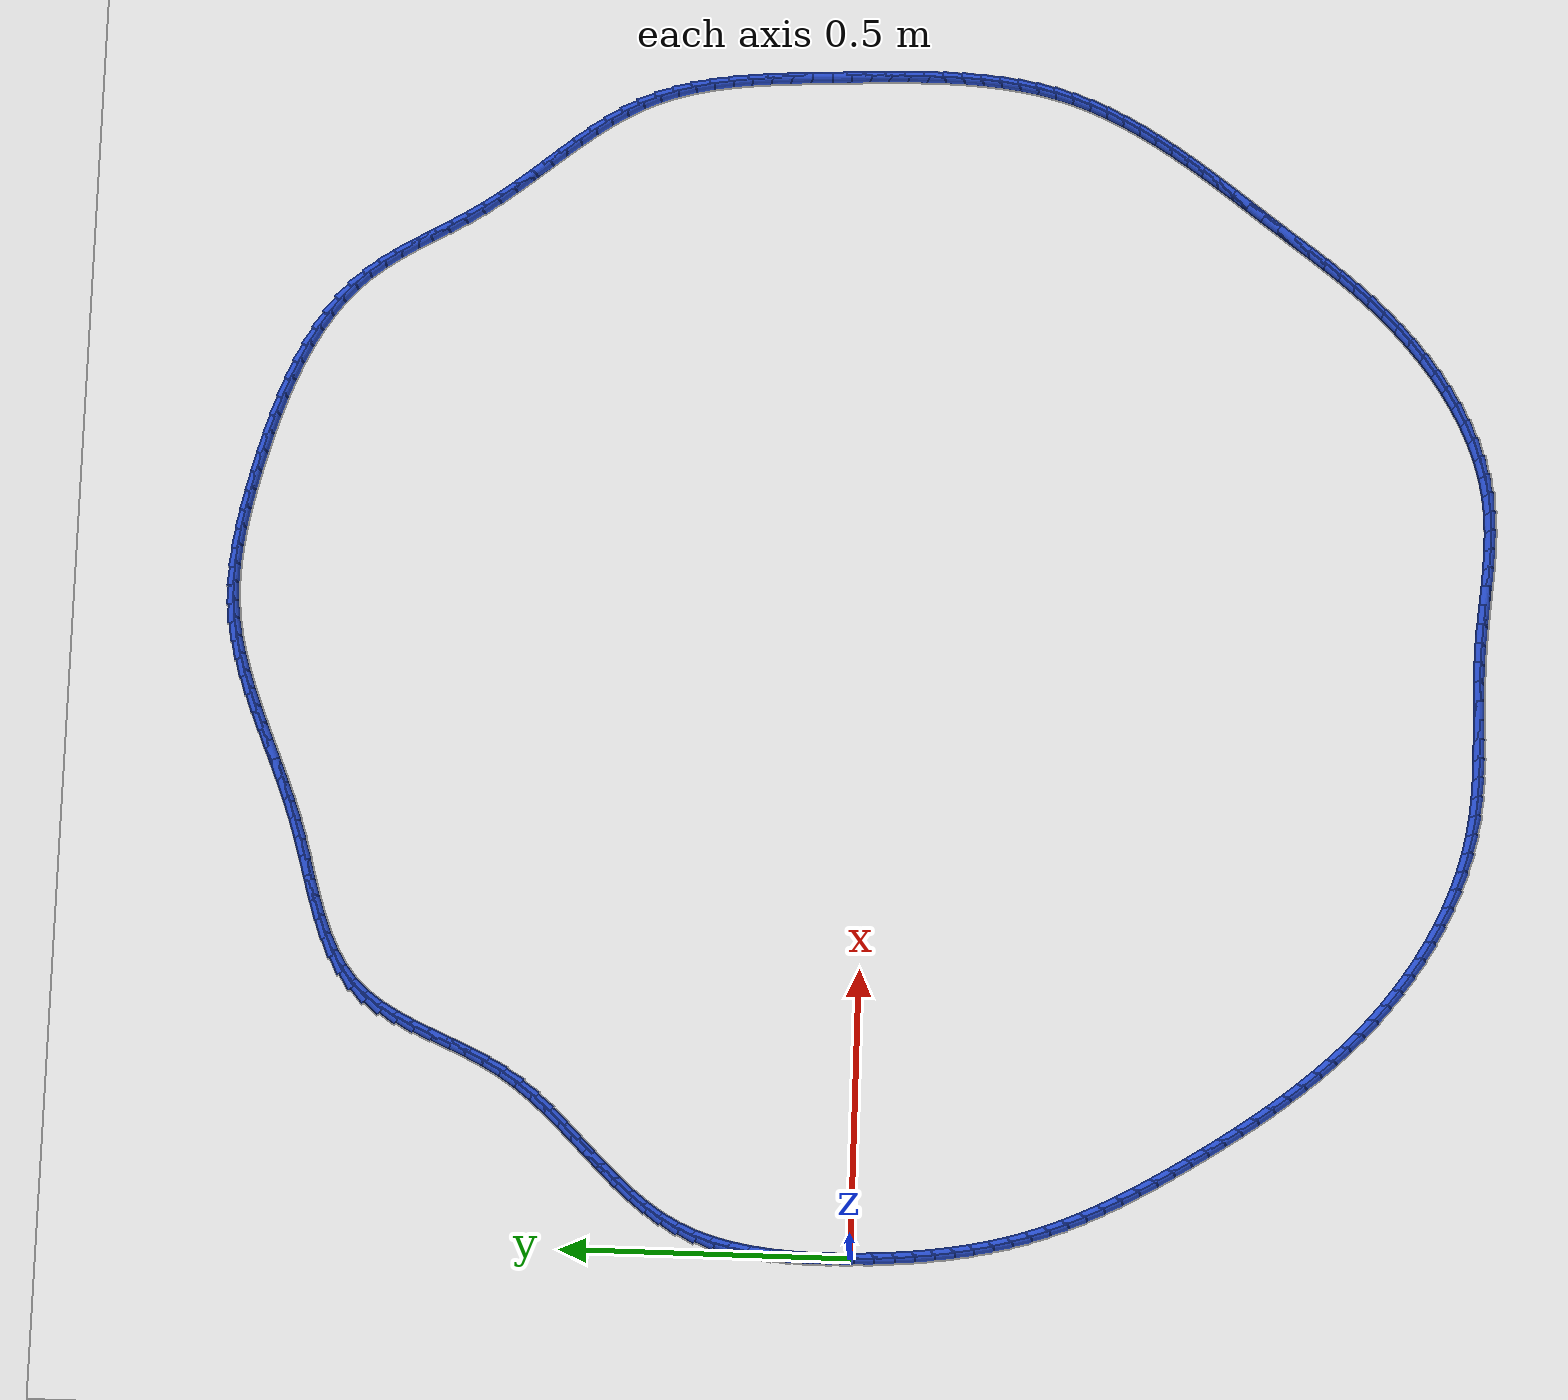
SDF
<sdf version="1.6">
 <world name="default">
  <light name="sun" type="directional">
   <pose>0 0 10 0 -0 0</pose>
   <diffuse>0.8 0.8 0.8 1</diffuse>
   <specular>0.2 0.2 0.2 1</specular>
   <attenuation>
    <range>1000</range>
    <constant>0.9</constant>
    <linear>0.01</linear>
    <quadratic>0.001</quadratic>
   </attenuation>
   <direction>-0.5 0.1 -0.9</direction>
  </light>
  <model name="ground_plane">
   <static>1</static>
   <link name="link">
    <collision name="collision">
     <geometry><plane><normal>0 0 1</normal><size>100 100</size></plane></geometry>
     <surface><friction><ode><mu>100</mu><mu2>50</mu2></ode></friction></surface>
    </collision>
    <visual name="visual">
     <cast_shadows>0</cast_shadows>
     <geometry><plane><normal>0 0 1</normal><size>100 100</size></plane></geometry>
     <material>
      <script><uri>file://media/materials/scripts/gazebo.material</uri><name>Gazebo/WhiteGlow</name></script>
     </material>
    </visual>
   </link>
  </model>
  <gravity>0 0 -9.8</gravity>
  <magnetic_field>6e-06 2.3e-05 -4.2e-05</magnetic_field>
  <atmosphere type="adiabatic"/>
  <physics name="default_physics" default="0" type="ode">
   <max_step_size>0.001</max_step_size>
   <real_time_factor>1</real_time_factor>
   <real_time_update_rate>1000</real_time_update_rate>
  </physics>
  <scene><ambient>0.4 0.4 0.4 1</ambient><background>0.7 0.7 0.7 1</background><shadows>1</shadows></scene>
  <spherical_coordinates>
   <surface_model>EARTH_WGS84</surface_model>
   <latitude_deg>0</latitude_deg>
   <longitude_deg>0</longitude_deg>
   <elevation>0</elevation>
   <heading_deg>0</heading_deg>
  </spherical_coordinates>
  <model name="line">
   <link name="link_0">
    <pose>1.1926223897340549e-17 4.85722573273506e-17 0.01 0 1.57 -1.5491836517026998</pose>
    <collision name="collision">
     <geometry><cylinder><radius>0.01</radius><length>0.08</length></cylinder></geometry>
    </collision>
    <visual name="visual">
     <material>
      <script><name>Gazebo/Blue</name><uri>file://media/materials/scripts/gazebo.material</uri></script>
     </material>
     <geometry><cylinder><radius>0.01</radius><length>0.08</length></cylinder></geometry>
    </visual>
   </link>
   <link name="link_1">
    <pose>-0.0007551033656751283 0.03493254709353343 0.01 0 1.57 1.567103791292674</pose>
    <collision name="collision">
     <geometry><cylinder><radius>0.01</radius><length>0.08</length></cylinder></geometry>
    </collision>
    <visual name="visual">
     <material>
      <script><name>Gazebo/Blue</name><uri>file://media/materials/scripts/gazebo.material</uri></script>
     </material>
     <geometry><cylinder><radius>0.01</radius><length>0.08</length></cylinder></geometry>
    </visual>
   </link>
   <link name="link_2">
    <pose>-0.0006257459633883587 0.06996452289628702 0.01 0 1.57 1.5350869671217766</pose>
    <collision name="collision">
     <geometry><cylinder><radius>0.01</radius><length>0.08</length></cylinder></geometry>
    </collision>
    <visual name="visual">
     <material>
      <script><name>Gazebo/Blue</name><uri>file://media/materials/scripts/gazebo.material</uri></script>
     </material>
     <geometry><cylinder><radius>0.01</radius><length>0.08</length></cylinder></geometry>
    </visual>
   </link>
   <link name="link_3">
    <pose>0.0006219113323401345 0.10488889403714445 0.01 0 1.57 1.4958196463155706</pose>
    <collision name="collision">
     <geometry><cylinder><radius>0.01</radius><length>0.08</length></cylinder></geometry>
    </collision>
    <visual name="visual">
     <material>
      <script><name>Gazebo/Blue</name><uri>file://media/materials/scripts/gazebo.material</uri></script>
     </material>
     <geometry><cylinder><radius>0.01</radius><length>0.08</length></cylinder></geometry>
    </visual>
   </link>
   <link name="link_4">
    <pose>0.0032217076469901657 0.13949862714498928 0.01 0 1.57 1.448614991465417</pose>
    <collision name="collision">
     <geometry><cylinder><radius>0.01</radius><length>0.08</length></cylinder></geometry>
    </collision>
    <visual name="visual">
     <material>
      <script><name>Gazebo/Blue</name><uri>file://media/materials/scripts/gazebo.material</uri></script>
     </material>
     <geometry><cylinder><radius>0.01</radius><length>0.08</length></cylinder></geometry>
    </visual>
   </link>
   <link name="link_5">
    <pose>0.0074074821060415505 0.1735866888487052 0.01 0 1.57 1.3926770391957781</pose>
    <collision name="collision">
     <geometry><cylinder><radius>0.01</radius><length>0.08</length></cylinder></geometry>
    </collision>
    <visual name="visual">
     <material>
      <script><name>Gazebo/Blue</name><uri>file://media/materials/scripts/gazebo.material</uri></script>
     </material>
     <geometry><cylinder><radius>0.01</radius><length>0.08</length></cylinder></geometry>
    </visual>
   </link>
   <link name="link_6">
    <pose>0.013413073834974101 0.20694604577717599 0.01 0 1.57 1.3271724449860847</pose>
    <collision name="collision">
     <geometry><cylinder><radius>0.01</radius><length>0.08</length></cylinder></geometry>
    </collision>
    <visual name="visual">
     <material>
      <script><name>Gazebo/Blue</name><uri>file://media/materials/scripts/gazebo.material</uri></script>
     </material>
     <geometry><cylinder><radius>0.01</radius><length>0.08</length></cylinder></geometry>
    </visual>
   </link>
   <link name="link_7">
    <pose>0.021472321959267637 0.23936966455928504 0.01 0 1.57 1.2513551835862469</pose>
    <collision name="collision">
     <geometry><cylinder><radius>0.01</radius><length>0.08</length></cylinder></geometry>
    </collision>
    <visual name="visual">
     <material>
      <script><name>Gazebo/Blue</name><uri>file://media/materials/scripts/gazebo.material</uri></script>
     </material>
     <geometry><cylinder><radius>0.01</radius><length>0.08</length></cylinder></geometry>
    </visual>
   </link>
   <link name="link_8">
    <pose>0.03181906560440195 0.2706505118239161 0.01 0 1.57 1.1647622745118291</pose>
    <collision name="collision">
     <geometry><cylinder><radius>0.01</radius><length>0.08</length></cylinder></geometry>
    </collision>
    <visual name="visual">
     <material>
      <script><name>Gazebo/Blue</name><uri>file://media/materials/scripts/gazebo.material</uri></script>
     </material>
     <geometry><cylinder><radius>0.01</radius><length>0.08</length></cylinder></geometry>
    </visual>
   </link>
   <link name="link_9">
    <pose>0.04468714389585687 0.3005815541999528 0.01 0 1.57 1.0689883449501432</pose>
    <collision name="collision">
     <geometry><cylinder><radius>0.01</radius><length>0.08</length></cylinder></geometry>
    </collision>
    <visual name="visual">
     <material>
      <script><name>Gazebo/Blue</name><uri>file://media/materials/scripts/gazebo.material</uri></script>
     </material>
     <geometry><cylinder><radius>0.01</radius><length>0.08</length></cylinder></geometry>
    </visual>
   </link>
   <link name="link_10">
    <pose>0.06027077677081624 0.32898502681090963 0.01 0 1.57 0.9801717202251125</pose>
    <collision name="collision">
     <geometry><cylinder><radius>0.01</radius><length>0.08</length></cylinder></geometry>
    </collision>
    <visual name="visual">
     <material>
      <script><name>Gazebo/Blue</name><uri>file://media/materials/scripts/gazebo.material</uri></script>
     </material>
     <geometry><cylinder><radius>0.01</radius><length>0.08</length></cylinder></geometry>
    </visual>
   </link>
   <link name="link_11">
    <pose>0.07836736968383333 0.35597630966927335 0.01 0 1.57 0.9082535807185579</pose>
    <collision name="collision">
     <geometry><cylinder><radius>0.01</radius><length>0.08</length></cylinder></geometry>
    </collision>
    <visual name="visual">
     <material>
      <script><name>Gazebo/Blue</name><uri>file://media/materials/scripts/gazebo.material</uri></script>
     </material>
     <geometry><cylinder><radius>0.01</radius><length>0.08</length></cylinder></geometry>
    </visual>
   </link>
   <link name="link_12">
    <pose>0.09854566436041864 0.3818397070743114 0.01 0 1.57 0.8535105636517946</pose>
    <collision name="collision">
     <geometry><cylinder><radius>0.01</radius><length>0.08</length></cylinder></geometry>
    </collision>
    <visual name="visual">
     <material>
      <script><name>Gazebo/Blue</name><uri>file://media/materials/scripts/gazebo.material</uri></script>
     </material>
     <geometry><cylinder><radius>0.01</radius><length>0.08</length></cylinder></geometry>
    </visual>
   </link>
   <link name="link_13">
    <pose>0.12037165102581888 0.40686155598356005 0.01 0 1.57 0.8154265885934336</pose>
    <collision name="collision">
     <geometry><cylinder><radius>0.01</radius><length>0.08</length></cylinder></geometry>
    </collision>
    <visual name="visual">
     <material>
      <script><name>Gazebo/Blue</name><uri>file://media/materials/scripts/gazebo.material</uri></script>
     </material>
     <geometry><cylinder><radius>0.01</radius><length>0.08</length></cylinder></geometry>
    </visual>
   </link>
   <link name="link_14">
    <pose>0.14341131990528067 0.43132819335455536 0.01 0 1.57 0.7932789726272074</pose>
    <collision name="collision">
     <geometry><cylinder><radius>0.01</radius><length>0.08</length></cylinder></geometry>
    </collision>
    <visual name="visual">
     <material>
      <script><name>Gazebo/Blue</name><uri>file://media/materials/scripts/gazebo.material</uri></script>
     </material>
     <geometry><cylinder><radius>0.01</radius><length>0.08</length></cylinder></geometry>
    </visual>
   </link>
   <link name="link_15">
    <pose>0.16723066122405064 0.45552595614483354 0.01 0 1.57 0.7864362148208434</pose>
    <collision name="collision">
     <geometry><cylinder><radius>0.01</radius><length>0.08</length></cylinder></geometry>
    </collision>
    <visual name="visual">
     <material>
      <script><name>Gazebo/Blue</name><uri>file://media/materials/scripts/gazebo.material</uri></script>
     </material>
     <geometry><cylinder><radius>0.01</radius><length>0.08</length></cylinder></geometry>
    </visual>
   </link>
   <link name="link_16">
    <pose>0.19139566520737553 0.47974118131193083 0.01 0 1.57 0.7945009354439476</pose>
    <collision name="collision">
     <geometry><cylinder><radius>0.01</radius><length>0.08</length></cylinder></geometry>
    </collision>
    <visual name="visual">
     <material>
      <script><name>Gazebo/Blue</name><uri>file://media/materials/scripts/gazebo.material</uri></script>
     </material>
     <geometry><cylinder><radius>0.01</radius><length>0.08</length></cylinder></geometry>
    </visual>
   </link>
   <link name="link_17">
    <pose>0.21547232208050202 0.5042602058133835 0.01 0 1.57 0.817338596577386</pose>
    <collision name="collision">
     <geometry><cylinder><radius>0.01</radius><length>0.08</length></cylinder></geometry>
    </collision>
    <visual name="visual">
     <material>
      <script><name>Gazebo/Blue</name><uri>file://media/materials/scripts/gazebo.material</uri></script>
     </material>
     <geometry><cylinder><radius>0.01</radius><length>0.08</length></cylinder></geometry>
    </visual>
   </link>
   <link name="link_18">
    <pose>0.23902662206867667 0.5293693666067275 0.01 0 1.57 0.8550148325637463</pose>
    <collision name="collision">
     <geometry><cylinder><radius>0.01</radius><length>0.08</length></cylinder></geometry>
    </collision>
    <visual name="visual">
     <material>
      <script><name>Gazebo/Blue</name><uri>file://media/materials/scripts/gazebo.material</uri></script>
     </material>
     <geometry><cylinder><radius>0.01</radius><length>0.08</length></cylinder></geometry>
    </visual>
   </link>
   <link name="link_19">
    <pose>0.26162455539714624 0.5553550006494993 0.01 0 1.57 0.9076428613577736</pose>
    <collision name="collision">
     <geometry><cylinder><radius>0.01</radius><length>0.08</length></cylinder></geometry>
    </collision>
    <visual name="visual">
     <material>
      <script><name>Gazebo/Blue</name><uri>file://media/materials/scripts/gazebo.material</uri></script>
     </material>
     <geometry><cylinder><radius>0.01</radius><length>0.08</length></cylinder></geometry>
    </visual>
   </link>
   <link name="link_20">
    <pose>0.28283211229115746 0.582503444899235 0.01 0 1.57 0.975132216110441</pose>
    <collision name="collision">
     <geometry><cylinder><radius>0.01</radius><length>0.08</length></cylinder></geometry>
    </collision>
    <visual name="visual">
     <material>
      <script><name>Gazebo/Blue</name><uri>file://media/materials/scripts/gazebo.material</uri></script>
     </material>
     <geometry><cylinder><radius>0.01</radius><length>0.08</length></cylinder></geometry>
    </visual>
   </link>
   <link name="link_21">
    <pose>0.3022152829759568 0.6111010363134706 0.01 0 1.57 1.051955359036336</pose>
    <collision name="collision">
     <geometry><cylinder><radius>0.01</radius><length>0.08</length></cylinder></geometry>
    </collision>
    <visual name="visual">
     <material>
      <script><name>Gazebo/Blue</name><uri>file://media/materials/scripts/gazebo.material</uri></script>
     </material>
     <geometry><cylinder><radius>0.01</radius><length>0.08</length></cylinder></geometry>
    </visual>
   </link>
   <link name="link_22">
    <pose>0.3194728886160618 0.6413232511368161 0.01 0 1.57 1.111703992971607</pose>
    <collision name="collision">
     <geometry><cylinder><radius>0.01</radius><length>0.08</length></cylinder></geometry>
    </collision>
    <visual name="visual">
     <material>
      <script><name>Gazebo/Blue</name><uri>file://media/materials/scripts/gazebo.material</uri></script>
     </material>
     <geometry><cylinder><radius>0.01</radius><length>0.08</length></cylinder></geometry>
    </visual>
   </link>
   <link name="link_23">
    <pose>0.3350105320771921 0.6727556855474687 0.01 0 1.57 1.1468354153574507</pose>
    <collision name="collision">
     <geometry><cylinder><radius>0.01</radius><length>0.08</length></cylinder></geometry>
    </collision>
    <visual name="visual">
     <material>
      <script><name>Gazebo/Blue</name><uri>file://media/materials/scripts/gazebo.material</uri></script>
     </material>
     <geometry><cylinder><radius>0.01</radius><length>0.08</length></cylinder></geometry>
    </visual>
   </link>
   <link name="link_24">
    <pose>0.34946796656684637 0.7047885138289672 0.01 0 1.57 1.1582037416370465</pose>
    <collision name="collision">
     <geometry><cylinder><radius>0.01</radius><length>0.08</length></cylinder></geometry>
    </collision>
    <visual name="visual">
     <material>
      <script><name>Gazebo/Blue</name><uri>file://media/materials/scripts/gazebo.material</uri></script>
     </material>
     <geometry><cylinder><radius>0.01</radius><length>0.08</length></cylinder></geometry>
    </visual>
   </link>
   <link name="link_25">
    <pose>0.3634850969562743 0.7368117836862714 0.01 0 1.57 1.1456927576206761</pose>
    <collision name="collision">
     <geometry><cylinder><radius>0.01</radius><length>0.08</length></cylinder></geometry>
    </collision>
    <visual name="visual">
     <material>
      <script><name>Gazebo/Blue</name><uri>file://media/materials/scripts/gazebo.material</uri></script>
     </material>
     <geometry><cylinder><radius>0.01</radius><length>0.08</length></cylinder></geometry>
    </visual>
   </link>
   <link name="link_26">
    <pose>0.3777018281167254 0.7682155428243408 0.01 0 1.57 1.1079685923999083</pose>
    <collision name="collision">
     <geometry><cylinder><radius>0.01</radius><length>0.08</length></cylinder></geometry>
    </collision>
    <visual name="visual">
     <material>
      <script><name>Gazebo/Blue</name><uri>file://media/materials/scripts/gazebo.material</uri></script>
     </material>
     <geometry><cylinder><radius>0.01</radius><length>0.08</length></cylinder></geometry>
    </visual>
   </link>
   <link name="link_27">
    <pose>0.39275806491944937 0.7983898389481353 0.01 0 1.57 1.042538447161997</pose>
    <collision name="collision">
     <geometry><cylinder><radius>0.01</radius><length>0.08</length></cylinder></geometry>
    </collision>
    <visual name="visual">
     <material>
      <script><name>Gazebo/Blue</name><uri>file://media/materials/scripts/gazebo.material</uri></script>
     </material>
     <geometry><cylinder><radius>0.01</radius><length>0.08</length></cylinder></geometry>
    </visual>
   </link>
   <link name="link_28">
    <pose>0.4092937122356956 0.826724719762614 0.01 0 1.57 0.9463308913781545</pose>
    <collision name="collision">
     <geometry><cylinder><radius>0.01</radius><length>0.08</length></cylinder></geometry>
    </collision>
    <visual name="visual">
     <material>
      <script><name>Gazebo/Blue</name><uri>file://media/materials/scripts/gazebo.material</uri></script>
     </material>
     <geometry><cylinder><radius>0.01</radius><length>0.08</length></cylinder></geometry>
    </visual>
   </link>
   <link name="link_29">
    <pose>0.42794867493671357 0.852610232972737 0.01 0 1.57 0.8173363148061481</pose>
    <collision name="collision">
     <geometry><cylinder><radius>0.01</radius><length>0.08</length></cylinder></geometry>
    </collision>
    <visual name="visual">
     <material>
      <script><name>Gazebo/Blue</name><uri>file://media/materials/scripts/gazebo.material</uri></script>
     </material>
     <geometry><cylinder><radius>0.01</radius><length>0.08</length></cylinder></geometry>
    </visual>
   </link>
   <link name="link_30">
    <pose>0.4493621611898803 0.8754371567631504 0.01 0 1.57 0.6704236372190755</pose>
    <collision name="collision">
     <geometry><cylinder><radius>0.01</radius><length>0.08</length></cylinder></geometry>
    </collision>
    <visual name="visual">
     <material>
      <script><name>Gazebo/Blue</name><uri>file://media/materials/scripts/gazebo.material</uri></script>
     </material>
     <geometry><cylinder><radius>0.01</radius><length>0.08</length></cylinder></geometry>
    </visual>
   </link>
   <link name="link_31">
    <pose>0.47389381687186866 0.894889384632855 0.01 0 1.57 0.5436318401502175</pose>
    <collision name="collision">
     <geometry><cylinder><radius>0.01</radius><length>0.08</length></cylinder></geometry>
    </collision>
    <visual name="visual">
     <material>
      <script><name>Gazebo/Blue</name><uri>file://media/materials/scripts/gazebo.material</uri></script>
     </material>
     <geometry><cylinder><radius>0.01</radius><length>0.08</length></cylinder></geometry>
    </visual>
   </link>
   <link name="link_32">
    <pose>0.5011973215342357 0.9113910012589488 0.01 0 1.57 0.4440254572823883</pose>
    <collision name="collision">
     <geometry><cylinder><radius>0.01</radius><length>0.08</length></cylinder></geometry>
    </collision>
    <visual name="visual">
     <material>
      <script><name>Gazebo/Blue</name><uri>file://media/materials/scripts/gazebo.material</uri></script>
     </material>
     <geometry><cylinder><radius>0.01</radius><length>0.08</length></cylinder></geometry>
    </visual>
   </link>
   <link name="link_33">
    <pose>0.5308166340523185 0.9254811311918286 0.01 0 1.57 0.37022620268007017</pose>
    <collision name="collision">
     <geometry><cylinder><radius>0.01</radius><length>0.08</length></cylinder></geometry>
    </collision>
    <visual name="visual">
     <material>
      <script><name>Gazebo/Blue</name><uri>file://media/materials/scripts/gazebo.material</uri></script>
     </material>
     <geometry><cylinder><radius>0.01</radius><length>0.08</length></cylinder></geometry>
    </visual>
   </link>
   <link name="link_34">
    <pose>0.5622957133014537 0.9376988989818918 0.01 0 1.57 0.31965790612082406</pose>
    <collision name="collision">
     <geometry><cylinder><radius>0.01</radius><length>0.08</length></cylinder></geometry>
    </collision>
    <visual name="visual">
     <material>
      <script><name>Gazebo/Blue</name><uri>file://media/materials/scripts/gazebo.material</uri></script>
     </material>
     <geometry><cylinder><radius>0.01</radius><length>0.08</length></cylinder></geometry>
    </visual>
   </link>
   <link name="link_35">
    <pose>0.5951785181569779 0.9485834291795345 0.01 0 1.57 0.28986337622023794</pose>
    <collision name="collision">
     <geometry><cylinder><radius>0.01</radius><length>0.08</length></cylinder></geometry>
    </collision>
    <visual name="visual">
     <material>
      <script><name>Gazebo/Blue</name><uri>file://media/materials/scripts/gazebo.material</uri></script>
     </material>
     <geometry><cylinder><radius>0.01</radius><length>0.08</length></cylinder></geometry>
    </visual>
   </link>
   <link name="link_36">
    <pose>0.6290090074942277 0.9586738463351536 0.01 0 1.57 0.27908347972789876</pose>
    <collision name="collision">
     <geometry><cylinder><radius>0.01</radius><length>0.08</length></cylinder></geometry>
    </collision>
    <visual name="visual">
     <material>
      <script><name>Gazebo/Blue</name><uri>file://media/materials/scripts/gazebo.material</uri></script>
     </material>
     <geometry><cylinder><radius>0.01</radius><length>0.08</length></cylinder></geometry>
    </visual>
   </link>
   <link name="link_37">
    <pose>0.6633311401885407 0.9685092749991465 0.01 0 1.57 0.2864357706763916</pose>
    <collision name="collision">
     <geometry><cylinder><radius>0.01</radius><length>0.08</length></cylinder></geometry>
    </collision>
    <visual name="visual">
     <material>
      <script><name>Gazebo/Blue</name><uri>file://media/materials/scripts/gazebo.material</uri></script>
     </material>
     <geometry><cylinder><radius>0.01</radius><length>0.08</length></cylinder></geometry>
    </visual>
   </link>
   <link name="link_38">
    <pose>0.6976888751152527 0.9786288397219088 0.01 0 1.57 0.3116604961665556</pose>
    <collision name="collision">
     <geometry><cylinder><radius>0.01</radius><length>0.08</length></cylinder></geometry>
    </collision>
    <visual name="visual">
     <material>
      <script><name>Gazebo/Blue</name><uri>file://media/materials/scripts/gazebo.material</uri></script>
     </material>
     <geometry><cylinder><radius>0.01</radius><length>0.08</length></cylinder></geometry>
    </visual>
   </link>
   <link name="link_39">
    <pose>0.7316313652078602 0.9895637306180698 0.01 0 1.57 0.34434486053398616</pose>
    <collision name="collision">
     <geometry><cylinder><radius>0.01</radius><length>0.08</length></cylinder></geometry>
    </collision>
    <visual name="visual">
     <material>
      <script><name>Gazebo/Blue</name><uri>file://media/materials/scripts/gazebo.material</uri></script>
     </material>
     <geometry><cylinder><radius>0.01</radius><length>0.08</length></cylinder></geometry>
    </visual>
   </link>
   <link name="link_40">
    <pose>0.7649299632712534 1.0015057055985463 0.01 0 1.57 0.36966709439179174</pose>
    <collision name="collision">
     <geometry><cylinder><radius>0.01</radius><length>0.08</length></cylinder></geometry>
    </collision>
    <visual name="visual">
     <material>
      <script><name>Gazebo/Blue</name><uri>file://media/materials/scripts/gazebo.material</uri></script>
     </material>
     <geometry><cylinder><radius>0.01</radius><length>0.08</length></cylinder></geometry>
    </visual>
   </link>
   <link name="link_41">
    <pose>0.797656981236301 1.0141867778466038 0.01 0 1.57 0.38636888372217</pose>
    <collision name="collision">
     <geometry><cylinder><radius>0.01</radius><length>0.08</length></cylinder></geometry>
    </collision>
    <visual name="visual">
     <material>
      <script><name>Gazebo/Blue</name><uri>file://media/materials/scripts/gazebo.material</uri></script>
     </material>
     <geometry><cylinder><radius>0.01</radius><length>0.08</length></cylinder></geometry>
    </visual>
   </link>
   <link name="link_42">
    <pose>0.8299061328758303 1.0273062671225364 0.01 0 1.57 0.3942600284666937</pose>
    <collision name="collision">
     <geometry><cylinder><radius>0.01</radius><length>0.08</length></cylinder></geometry>
    </collision>
    <visual name="visual">
     <material>
      <script><name>Gazebo/Blue</name><uri>file://media/materials/scripts/gazebo.material</uri></script>
     </material>
     <geometry><cylinder><radius>0.01</radius><length>0.08</length></cylinder></geometry>
    </visual>
   </link>
   <link name="link_43">
    <pose>0.8617711319626692 1.0405634931866383 0.01 0 1.57 0.39312265436274746</pose>
    <collision name="collision">
     <geometry><cylinder><radius>0.01</radius><length>0.08</length></cylinder></geometry>
    </collision>
    <visual name="visual">
     <material>
      <script><name>Gazebo/Blue</name><uri>file://media/materials/scripts/gazebo.material</uri></script>
     </material>
     <geometry><cylinder><radius>0.01</radius><length>0.08</length></cylinder></geometry>
    </visual>
   </link>
   <link name="link_44">
    <pose>0.8933456922696452 1.0536577757992052 0.01 0 1.57 0.3826893158773114</pose>
    <collision name="collision">
     <geometry><cylinder><radius>0.01</radius><length>0.08</length></cylinder></geometry>
    </collision>
    <visual name="visual">
     <material>
      <script><name>Gazebo/Blue</name><uri>file://media/materials/scripts/gazebo.material</uri></script>
     </material>
     <geometry><cylinder><radius>0.01</radius><length>0.08</length></cylinder></geometry>
    </visual>
   </link>
   <link name="link_45">
    <pose>0.9247235275695861 1.0662884347205301 0.01 0 1.57 0.3626418083650684</pose>
    <collision name="collision">
     <geometry><cylinder><radius>0.01</radius><length>0.08</length></cylinder></geometry>
    </collision>
    <visual name="visual">
     <material>
      <script><name>Gazebo/Blue</name><uri>file://media/materials/scripts/gazebo.material</uri></script>
     </material>
     <geometry><cylinder><radius>0.01</radius><length>0.08</length></cylinder></geometry>
    </visual>
   </link>
   <link name="link_46">
    <pose>0.9559983516353194 1.0781547897109087 0.01 0 1.57 0.33263547977446745</pose>
    <collision name="collision">
     <geometry><cylinder><radius>0.01</radius><length>0.08</length></cylinder></geometry>
    </collision>
    <visual name="visual">
     <material>
      <script><name>Gazebo/Blue</name><uri>file://media/materials/scripts/gazebo.material</uri></script>
     </material>
     <geometry><cylinder><radius>0.01</radius><length>0.08</length></cylinder></geometry>
    </visual>
   </link>
   <link name="link_47">
    <pose>0.9872638782396724 1.0889561605306346 0.01 0 1.57 0.29235565163840377</pose>
    <collision name="collision">
     <geometry><cylinder><radius>0.01</radius><length>0.08</length></cylinder></geometry>
    </collision>
    <visual name="visual">
     <material>
      <script><name>Gazebo/Blue</name><uri>file://media/materials/scripts/gazebo.material</uri></script>
     </material>
     <geometry><cylinder><radius>0.01</radius><length>0.08</length></cylinder></geometry>
    </visual>
   </link>
   <link name="link_48">
    <pose>1.018613821155473 1.0983918669400026 0.01 0 1.57 0.2416128228604303</pose>
    <collision name="collision">
     <geometry><cylinder><radius>0.01</radius><length>0.08</length></cylinder></geometry>
    </collision>
    <visual name="visual">
     <material>
      <script><name>Gazebo/Blue</name><uri>file://media/materials/scripts/gazebo.material</uri></script>
     </material>
     <geometry><cylinder><radius>0.01</radius><length>0.08</length></cylinder></geometry>
    </visual>
   </link>
   <link name="link_49">
    <pose>1.0501418941555487 1.106161228699307 0.01 0 1.57 0.18047848449558837</pose>
    <collision name="collision">
     <geometry><cylinder><radius>0.01</radius><length>0.08</length></cylinder></geometry>
    </collision>
    <visual name="visual">
     <material>
      <script><name>Gazebo/Blue</name><uri>file://media/materials/scripts/gazebo.material</uri></script>
     </material>
     <geometry><cylinder><radius>0.01</radius><length>0.08</length></cylinder></geometry>
    </visual>
   </link>
   <link name="link_50">
    <pose>1.0819418110127272 1.1119635655688427 0.01 0 1.57 0.1095363059471987</pose>
    <collision name="collision">
     <geometry><cylinder><radius>0.01</radius><length>0.08</length></cylinder></geometry>
    </collision>
    <visual name="visual">
     <material>
      <script><name>Gazebo/Blue</name><uri>file://media/materials/scripts/gazebo.material</uri></script>
     </material>
     <geometry><cylinder><radius>0.01</radius><length>0.08</length></cylinder></geometry>
    </visual>
   </link>
   <link name="link_51">
    <pose>1.1141065732753948 1.1155009334898973 0.01 0 1.57 0.03584947656787952</pose>
    <collision name="collision">
     <geometry><cylinder><radius>0.01</radius><length>0.08</length></cylinder></geometry>
    </collision>
    <visual name="visual">
     <material>
      <script><name>Gazebo/Blue</name><uri>file://media/materials/scripts/gazebo.material</uri></script>
     </material>
     <geometry><cylinder><radius>0.01</radius><length>0.08</length></cylinder></geometry>
    </visual>
   </link>
   <link name="link_52">
    <pose>1.146678751920672 1.1166691295372233 0.01 0 1.57 -0.029940667456427227</pose>
    <collision name="collision">
     <geometry><cylinder><radius>0.01</radius><length>0.08</length></cylinder></geometry>
    </collision>
    <visual name="visual">
     <material>
      <script><name>Gazebo/Blue</name><uri>file://media/materials/scripts/gazebo.material</uri></script>
     </material>
     <geometry><cylinder><radius>0.01</radius><length>0.08</length></cylinder></geometry>
    </visual>
   </link>
   <link name="link_53">
    <pose>1.1796179706755174 1.1156826125389854 0.01 0 1.57 -0.08688996958565974</pose>
    <collision name="collision">
     <geometry><cylinder><radius>0.01</radius><length>0.08</length></cylinder></geometry>
    </collision>
    <visual name="visual">
     <material>
      <script><name>Gazebo/Blue</name><uri>file://media/materials/scripts/gazebo.material</uri></script>
     </material>
     <geometry><cylinder><radius>0.01</radius><length>0.08</length></cylinder></geometry>
    </visual>
   </link>
   <link name="link_54">
    <pose>1.2128761285576757 1.1127855176462742 0.01 0 1.57 -0.13527594651336852</pose>
    <collision name="collision">
     <geometry><cylinder><radius>0.01</radius><length>0.08</length></cylinder></geometry>
    </collision>
    <visual name="visual">
     <material>
      <script><name>Gazebo/Blue</name><uri>file://media/materials/scripts/gazebo.material</uri></script>
     </material>
     <geometry><cylinder><radius>0.01</radius><length>0.08</length></cylinder></geometry>
    </visual>
   </link>
   <link name="link_55">
    <pose>1.246405124584893 1.1082219800101811 0.01 0 1.57 -0.17552421466811913</pose>
    <collision name="collision">
     <geometry><cylinder><radius>0.01</radius><length>0.08</length></cylinder></geometry>
    </collision>
    <visual name="visual">
     <material>
      <script><name>Gazebo/Blue</name><uri>file://media/materials/scripts/gazebo.material</uri></script>
     </material>
     <geometry><cylinder><radius>0.01</radius><length>0.08</length></cylinder></geometry>
    </visual>
   </link>
   <link name="link_56">
    <pose>1.2801568577749152 1.1022361347817975 0.01 0 1.57 -0.20810648096598622</pose>
    <collision name="collision">
     <geometry><cylinder><radius>0.01</radius><length>0.08</length></cylinder></geometry>
    </collision>
    <visual name="visual">
     <material>
      <script><name>Gazebo/Blue</name><uri>file://media/materials/scripts/gazebo.material</uri></script>
     </material>
     <geometry><cylinder><radius>0.01</radius><length>0.08</length></cylinder></geometry>
    </visual>
   </link>
   <link name="link_57">
    <pose>1.3140832271454888 1.0950721171122149 0.01 0 1.57 -0.23347138581808904</pose>
    <collision name="collision">
     <geometry><cylinder><radius>0.01</radius><length>0.08</length></cylinder></geometry>
    </collision>
    <visual name="visual">
     <material>
      <script><name>Gazebo/Blue</name><uri>file://media/materials/scripts/gazebo.material</uri></script>
     </material>
     <geometry><cylinder><radius>0.01</radius><length>0.08</length></cylinder></geometry>
    </visual>
   </link>
   <link name="link_58">
    <pose>1.3481361317143583 1.0869740621525237 0.01 0 1.57 -0.2523281253426804</pose>
    <collision name="collision">
     <geometry><cylinder><radius>0.01</radius><length>0.08</length></cylinder></geometry>
    </collision>
    <visual name="visual">
     <material>
      <script><name>Gazebo/Blue</name><uri>file://media/materials/scripts/gazebo.material</uri></script>
     </material>
     <geometry><cylinder><radius>0.01</radius><length>0.08</length></cylinder></geometry>
    </visual>
   </link>
   <link name="link_59">
    <pose>1.3822631749105763 1.0781753146162425 0.01 0 1.57 -0.2708769066060048</pose>
    <collision name="collision">
     <geometry><cylinder><radius>0.01</radius><length>0.08</length></cylinder></geometry>
    </collision>
    <visual name="visual">
     <material>
      <script><name>Gazebo/Blue</name><uri>file://media/materials/scripts/gazebo.material</uri></script>
     </material>
     <geometry><cylinder><radius>0.01</radius><length>0.08</length></cylinder></geometry>
    </visual>
   </link>
   <link name="link_60">
    <pose>1.4163341357294066 1.0687137257108612 0.01 0 1.57 -0.29448013508410376</pose>
    <collision name="collision">
     <geometry><cylinder><radius>0.01</radius><length>0.08</length></cylinder></geometry>
    </collision>
    <visual name="visual">
     <material>
      <script><name>Gazebo/Blue</name><uri>file://media/materials/scripts/gazebo.material</uri></script>
     </material>
     <geometry><cylinder><radius>0.01</radius><length>0.08</length></cylinder></geometry>
    </visual>
   </link>
   <link name="link_61">
    <pose>1.450151096593502 1.058457094133596 0.01 0 1.57 -0.32360046700444534</pose>
    <collision name="collision">
     <geometry><cylinder><radius>0.01</radius><length>0.08</length></cylinder></geometry>
    </collision>
    <visual name="visual">
     <material>
      <script><name>Gazebo/Blue</name><uri>file://media/materials/scripts/gazebo.material</uri></script>
     </material>
     <geometry><cylinder><radius>0.01</radius><length>0.08</length></cylinder></geometry>
    </visual>
   </link>
   <link name="link_62">
    <pose>1.4835138822596006 1.047267547367574 0.01 0 1.57 -0.3586278318809204</pose>
    <collision name="collision">
     <geometry><cylinder><radius>0.01</radius><length>0.08</length></cylinder></geometry>
    </collision>
    <visual name="visual">
     <material>
      <script><name>Gazebo/Blue</name><uri>file://media/materials/scripts/gazebo.material</uri></script>
     </material>
     <geometry><cylinder><radius>0.01</radius><length>0.08</length></cylinder></geometry>
    </visual>
   </link>
   <link name="link_63">
    <pose>1.5162223174844387 1.0350072128959238 0.01 0 1.57 -0.4000366925408505</pose>
    <collision name="collision">
     <geometry><cylinder><radius>0.01</radius><length>0.08</length></cylinder></geometry>
    </collision>
    <visual name="visual">
     <material>
      <script><name>Gazebo/Blue</name><uri>file://media/materials/scripts/gazebo.material</uri></script>
     </material>
     <geometry><cylinder><radius>0.01</radius><length>0.08</length></cylinder></geometry>
    </visual>
   </link>
   <link name="link_64">
    <pose>1.5480762270247537 1.021538218201773 0.01 0 1.57 -0.4483616194460339</pose>
    <collision name="collision">
     <geometry><cylinder><radius>0.01</radius><length>0.08</length></cylinder></geometry>
    </collision>
    <visual name="visual">
     <material>
      <script><name>Gazebo/Blue</name><uri>file://media/materials/scripts/gazebo.material</uri></script>
     </material>
     <geometry><cylinder><radius>0.01</radius><length>0.08</length></cylinder></geometry>
    </visual>
   </link>
   <link name="link_65">
    <pose>1.5788754356372832 1.00672269076825 0.01 0 1.57 -0.504155876282202</pose>
    <collision name="collision">
     <geometry><cylinder><radius>0.01</radius><length>0.08</length></cylinder></geometry>
    </collision>
    <visual name="visual">
     <material>
      <script><name>Gazebo/Blue</name><uri>file://media/materials/scripts/gazebo.material</uri></script>
     </material>
     <geometry><cylinder><radius>0.01</radius><length>0.08</length></cylinder></geometry>
    </visual>
   </link>
   <link name="link_66">
    <pose>1.6084197680787642 0.9904227580784825 0.01 0 1.57 -0.5679246658376544</pose>
    <collision name="collision">
     <geometry><cylinder><radius>0.01</radius><length>0.08</length></cylinder></geometry>
    </collision>
    <visual name="visual">
     <material>
      <script><name>Gazebo/Blue</name><uri>file://media/materials/scripts/gazebo.material</uri></script>
     </material>
     <geometry><cylinder><radius>0.01</radius><length>0.08</length></cylinder></geometry>
    </visual>
   </link>
   <link name="link_67">
    <pose>1.6365090491059342 0.9725005476155988 0.01 0 1.57 -0.6400255272742617</pose>
    <collision name="collision">
     <geometry><cylinder><radius>0.01</radius><length>0.08</length></cylinder></geometry>
    </collision>
    <visual name="visual">
     <material>
      <script><name>Gazebo/Blue</name><uri>file://media/materials/scripts/gazebo.material</uri></script>
     </material>
     <geometry><cylinder><radius>0.01</radius><length>0.08</length></cylinder></geometry>
    </visual>
   </link>
   <link name="link_68">
    <pose>1.6629431034755304 0.9528181868627268 0.01 0 1.57 -0.7205340963091029</pose>
    <collision name="collision">
     <geometry><cylinder><radius>0.01</radius><length>0.08</length></cylinder></geometry>
    </collision>
    <visual name="visual">
     <material>
      <script><name>Gazebo/Blue</name><uri>file://media/materials/scripts/gazebo.material</uri></script>
     </material>
     <geometry><cylinder><radius>0.01</radius><length>0.08</length></cylinder></geometry>
    </visual>
   </link>
   <link name="link_69">
    <pose>1.6875217559442903 0.9312378033029945 0.01 0 1.57 -0.8090737651607606</pose>
    <collision name="collision">
     <geometry><cylinder><radius>0.01</radius><length>0.08</length></cylinder></geometry>
    </collision>
    <visual name="visual">
     <material>
      <script><name>Gazebo/Blue</name><uri>file://media/materials/scripts/gazebo.material</uri></script>
     </material>
     <geometry><cylinder><radius>0.01</radius><length>0.08</length></cylinder></geometry>
    </visual>
   </link>
   <link name="link_70">
    <pose>1.7100451761367708 0.907621800351638 0.01 0 1.57 -0.8977581351296104</pose>
    <collision name="collision">
     <geometry><cylinder><radius>0.01</radius><length>0.08</length></cylinder></geometry>
    </collision>
    <visual name="visual">
     <material>
      <script><name>Gazebo/Blue</name><uri>file://media/materials/scripts/gazebo.material</uri></script>
     </material>
     <geometry><cylinder><radius>0.01</radius><length>0.08</length></cylinder></geometry>
    </visual>
   </link>
   <link name="link_71">
    <pose>1.7304912652548834 0.8819747861933385 0.01 0 1.57 -0.9673729879554962</pose>
    <collision name="collision">
     <geometry><cylinder><radius>0.01</radius><length>0.08</length></cylinder></geometry>
    </collision>
    <visual name="visual">
     <material>
      <script><name>Gazebo/Blue</name><uri>file://media/materials/scripts/gazebo.material</uri></script>
     </material>
     <geometry><cylinder><radius>0.01</radius><length>0.08</length></cylinder></geometry>
    </visual>
   </link>
   <link name="link_72">
    <pose>1.7493053344820453 0.8546753483002204 0.01 0 1.57 -1.015154472029807</pose>
    <collision name="collision">
     <geometry><cylinder><radius>0.01</radius><length>0.08</length></cylinder></geometry>
    </collision>
    <visual name="visual">
     <material>
      <script><name>Gazebo/Blue</name><uri>file://media/materials/scripts/gazebo.material</uri></script>
     </material>
     <geometry><cylinder><radius>0.01</radius><length>0.08</length></cylinder></geometry>
    </visual>
   </link>
   <link name="link_73">
    <pose>1.7670086167516006 0.8261628198774149 0.01 0 1.57 -1.0419563552210067</pose>
    <collision name="collision">
     <geometry><cylinder><radius>0.01</radius><length>0.08</length></cylinder></geometry>
    </collision>
    <visual name="visual">
     <material>
      <script><name>Gazebo/Blue</name><uri>file://media/materials/scripts/gazebo.material</uri></script>
     </material>
     <geometry><cylinder><radius>0.01</radius><length>0.08</length></cylinder></geometry>
    </visual>
   </link>
   <link name="link_74">
    <pose>1.7841223449968948 0.7968765341300521 0.01 0 1.57 -1.0486196228915903</pose>
    <collision name="collision">
     <geometry><cylinder><radius>0.01</radius><length>0.08</length></cylinder></geometry>
    </collision>
    <visual name="visual">
     <material>
      <script><name>Gazebo/Blue</name><uri>file://media/materials/scripts/gazebo.material</uri></script>
     </material>
     <geometry><cylinder><radius>0.01</radius><length>0.08</length></cylinder></geometry>
    </visual>
   </link>
   <link name="link_75">
    <pose>1.8011677521512734 0.7672558242632626 0.01 0 1.57 -1.0356538628466374</pose>
    <collision name="collision">
     <geometry><cylinder><radius>0.01</radius><length>0.08</length></cylinder></geometry>
    </collision>
    <visual name="visual">
     <material>
      <script><name>Gazebo/Blue</name><uri>file://media/materials/scripts/gazebo.material</uri></script>
     </material>
     <geometry><cylinder><radius>0.01</radius><length>0.08</length></cylinder></geometry>
    </visual>
   </link>
   <link name="link_76">
    <pose>1.8186660711480822 0.7377400234821772 0.01 0 1.57 -1.0031944326292686</pose>
    <collision name="collision">
     <geometry><cylinder><radius>0.01</radius><length>0.08</length></cylinder></geometry>
    </collision>
    <visual name="visual">
     <material>
      <script><name>Gazebo/Blue</name><uri>file://media/materials/scripts/gazebo.material</uri></script>
     </material>
     <geometry><cylinder><radius>0.01</radius><length>0.08</length></cylinder></geometry>
    </visual>
   </link>
   <link name="link_77">
    <pose>1.83713820705642 0.7087682319937668 0.01 0 1.57 -0.9587220980473151</pose>
    <collision name="collision">
     <geometry><cylinder><radius>0.01</radius><length>0.08</length></cylinder></geometry>
    </collision>
    <visual name="visual">
     <material>
      <script><name>Gazebo/Blue</name><uri>file://media/materials/scripts/gazebo.material</uri></script>
     </material>
     <geometry><cylinder><radius>0.01</radius><length>0.08</length></cylinder></geometry>
    </visual>
   </link>
   <link name="link_78">
    <pose>1.8568925736214246 0.680628542116698 0.01 0 1.57 -0.9227784637114881</pose>
    <collision name="collision">
     <geometry><cylinder><radius>0.01</radius><length>0.08</length></cylinder></geometry>
    </collision>
    <visual name="visual">
     <material>
      <script><name>Gazebo/Blue</name><uri>file://media/materials/scripts/gazebo.material</uri></script>
     </material>
     <geometry><cylinder><radius>0.01</radius><length>0.08</length></cylinder></geometry>
    </visual>
   </link>
   <link name="link_79">
    <pose>1.8776595365178956 0.6531982537814465 0.01 0 1.57 -0.8987270306589904</pose>
    <collision name="collision">
     <geometry><cylinder><radius>0.01</radius><length>0.08</length></cylinder></geometry>
    </collision>
    <visual name="visual">
     <material>
      <script><name>Gazebo/Blue</name><uri>file://media/materials/scripts/gazebo.material</uri></script>
     </material>
     <geometry><cylinder><radius>0.01</radius><length>0.08</length></cylinder></geometry>
    </visual>
   </link>
   <link name="link_80">
    <pose>1.8990720943488149 0.6262854725832504 0.01 0 1.57 -0.8864649699935222</pose>
    <collision name="collision">
     <geometry><cylinder><radius>0.01</radius><length>0.08</length></cylinder></geometry>
    </collision>
    <visual name="visual">
     <material>
      <script><name>Gazebo/Blue</name><uri>file://media/materials/scripts/gazebo.material</uri></script>
     </material>
     <geometry><cylinder><radius>0.01</radius><length>0.08</length></cylinder></geometry>
    </visual>
   </link>
   <link name="link_81">
    <pose>1.9207632457171666 0.5996983041173483 0.01 0 1.57 -0.8859956596788255</pose>
    <collision name="collision">
     <geometry><cylinder><radius>0.01</radius><length>0.08</length></cylinder></geometry>
    </collision>
    <visual name="visual">
     <material>
      <script><name>Gazebo/Blue</name><uri>file://media/materials/scripts/gazebo.material</uri></script>
     </material>
     <geometry><cylinder><radius>0.01</radius><length>0.08</length></cylinder></geometry>
    </visual>
   </link>
   <link name="link_82">
    <pose>1.9423659892259335 0.5732448539789776 0.01 0 1.57 -0.8974822185752316</pose>
    <collision name="collision">
     <geometry><cylinder><radius>0.01</radius><length>0.08</length></cylinder></geometry>
    </collision>
    <visual name="visual">
     <material>
      <script><name>Gazebo/Blue</name><uri>file://media/materials/scripts/gazebo.material</uri></script>
     </material>
     <geometry><cylinder><radius>0.01</radius><length>0.08</length></cylinder></geometry>
    </visual>
   </link>
   <link name="link_83">
    <pose>1.9635133234780977 0.5467332277633766 0.01 0 1.57 -0.9212567549371053</pose>
    <collision name="collision">
     <geometry><cylinder><radius>0.01</radius><length>0.08</length></cylinder></geometry>
    </collision>
    <visual name="visual">
     <material>
      <script><name>Gazebo/Blue</name><uri>file://media/materials/scripts/gazebo.material</uri></script>
     </material>
     <geometry><cylinder><radius>0.01</radius><length>0.08</length></cylinder></geometry>
    </visual>
   </link>
   <link name="link_84">
    <pose>1.9838382470766431 0.5199715310657844 0.01 0 1.57 -0.9577809125137218</pose>
    <collision name="collision">
     <geometry><cylinder><radius>0.01</radius><length>0.08</length></cylinder></geometry>
    </collision>
    <visual name="visual">
     <material>
      <script><name>Gazebo/Blue</name><uri>file://media/materials/scripts/gazebo.material</uri></script>
     </material>
     <geometry><cylinder><radius>0.01</radius><length>0.08</length></cylinder></geometry>
    </visual>
   </link>
   <link name="link_85">
    <pose>2.0029737586245524 0.49276786948143775 0.01 0 1.57 -1.007544113193847</pose>
    <collision name="collision">
     <geometry><cylinder><radius>0.01</radius><length>0.08</length></cylinder></geometry>
    </collision>
    <visual name="visual">
     <material>
      <script><name>Gazebo/Blue</name><uri>file://media/materials/scripts/gazebo.material</uri></script>
     </material>
     <geometry><cylinder><radius>0.01</radius><length>0.08</length></cylinder></geometry>
    </visual>
   </link>
   <link name="link_86">
    <pose>2.020552856724809 0.4649303486055757 0.01 0 1.57 -1.0708805650021231</pose>
    <collision name="collision">
     <geometry><cylinder><radius>0.01</radius><length>0.08</length></cylinder></geometry>
    </collision>
    <visual name="visual">
     <material>
      <script><name>Gazebo/Blue</name><uri>file://media/materials/scripts/gazebo.material</uri></script>
     </material>
     <geometry><cylinder><radius>0.01</radius><length>0.08</length></cylinder></geometry>
    </visual>
   </link>
   <link name="link_87">
    <pose>2.036208539980396 0.43626707403343595 0.01 0 1.57 -1.1472410660836165</pose>
    <collision name="collision">
     <geometry><cylinder><radius>0.01</radius><length>0.08</length></cylinder></geometry>
    </collision>
    <visual name="visual">
     <material>
      <script><name>Gazebo/Blue</name><uri>file://media/materials/scripts/gazebo.material</uri></script>
     </material>
     <geometry><cylinder><radius>0.01</radius><length>0.08</length></cylinder></geometry>
    </visual>
   </link>
   <link name="link_88">
    <pose>2.0495870495548947 0.406592683746153 0.01 0 1.57 -1.2255441221676449</pose>
    <collision name="collision">
     <geometry><cylinder><radius>0.01</radius><length>0.08</length></cylinder></geometry>
    </collision>
    <visual name="visual">
     <material>
      <script><name>Gazebo/Blue</name><uri>file://media/materials/scripts/gazebo.material</uri></script>
     </material>
     <geometry><cylinder><radius>0.01</radius><length>0.08</length></cylinder></geometry>
    </visual>
   </link>
   <link name="link_89">
    <pose>2.0606364382333635 0.37587069554040914 0.01 0 1.57 -1.294732867674398</pose>
    <collision name="collision">
     <geometry><cylinder><radius>0.01</radius><length>0.08</length></cylinder></geometry>
    </collision>
    <visual name="visual">
     <material>
      <script><name>Gazebo/Blue</name><uri>file://media/materials/scripts/gazebo.material</uri></script>
     </material>
     <geometry><cylinder><radius>0.01</radius><length>0.08</length></cylinder></geometry>
    </visual>
   </link>
   <link name="link_90">
    <pose>2.0696050410072577 0.3442127525875256 0.01 0 1.57 -1.3541168987590173</pose>
    <collision name="collision">
     <geometry><cylinder><radius>0.01</radius><length>0.08</length></cylinder></geometry>
    </collision>
    <visual name="visual">
     <material>
      <script><name>Gazebo/Blue</name><uri>file://media/materials/scripts/gazebo.material</uri></script>
     </material>
     <geometry><cylinder><radius>0.01</radius><length>0.08</length></cylinder></geometry>
    </visual>
   </link>
   <link name="link_91">
    <pose>2.0767541295431444 0.31173687955531665 0.01 0 1.57 -1.4038430804448196</pose>
    <collision name="collision">
     <geometry><cylinder><radius>0.01</radius><length>0.08</length></cylinder></geometry>
    </collision>
    <visual name="visual">
     <material>
      <script><name>Gazebo/Blue</name><uri>file://media/materials/scripts/gazebo.material</uri></script>
     </material>
     <geometry><cylinder><radius>0.01</radius><length>0.08</length></cylinder></geometry>
    </visual>
   </link>
   <link name="link_92">
    <pose>2.08234497550759 0.27856110111159677 0.01 0 1.57 -1.4442786596421489</pose>
    <collision name="collision">
     <geometry><cylinder><radius>0.01</radius><length>0.08</length></cylinder></geometry>
    </collision>
    <visual name="visual">
     <material>
      <script><name>Gazebo/Blue</name><uri>file://media/materials/scripts/gazebo.material</uri></script>
     </material>
     <geometry><cylinder><radius>0.01</radius><length>0.08</length></cylinder></geometry>
    </visual>
   </link>
   <link name="link_93">
    <pose>2.0866388505671605 0.2448034419241805 0.01 0 1.57 -1.4758740457370778</pose>
    <collision name="collision">
     <geometry><cylinder><radius>0.01</radius><length>0.08</length></cylinder></geometry>
    </collision>
    <visual name="visual">
     <material>
      <script><name>Gazebo/Blue</name><uri>file://media/materials/scripts/gazebo.material</uri></script>
     </material>
     <geometry><cylinder><radius>0.01</radius><length>0.08</length></cylinder></geometry>
    </visual>
   </link>
   <link name="link_94">
    <pose>2.0898970263884222 0.21058192666088207 0.01 0 1.57 -1.4990671564346123</pose>
    <collision name="collision">
     <geometry><cylinder><radius>0.01</radius><length>0.08</length></cylinder></geometry>
    </collision>
    <visual name="visual">
     <material>
      <script><name>Gazebo/Blue</name><uri>file://media/materials/scripts/gazebo.material</uri></script>
     </material>
     <geometry><cylinder><radius>0.01</radius><length>0.08</length></cylinder></geometry>
    </visual>
   </link>
   <link name="link_95">
    <pose>2.0923807746379413 0.17601457998951606 0.01 0 1.57 -1.5142226561445344</pose>
    <collision name="collision">
     <geometry><cylinder><radius>0.01</radius><length>0.08</length></cylinder></geometry>
    </collision>
    <visual name="visual">
     <material>
      <script><name>Gazebo/Blue</name><uri>file://media/materials/scripts/gazebo.material</uri></script>
     </material>
     <geometry><cylinder><radius>0.01</radius><length>0.08</length></cylinder></geometry>
    </visual>
   </link>
   <link name="link_96">
    <pose>2.0943513669822846 0.14121942657789727 0.01 0 1.57 -1.5215963764247071</pose>
    <collision name="collision">
     <geometry><cylinder><radius>0.01</radius><length>0.08</length></cylinder></geometry>
    </collision>
    <visual name="visual">
     <material>
      <script><name>Gazebo/Blue</name><uri>file://media/materials/scripts/gazebo.material</uri></script>
     </material>
     <geometry><cylinder><radius>0.01</radius><length>0.08</length></cylinder></geometry>
    </visual>
   </link>
   <link name="link_97">
    <pose>2.096070075088019 0.10631449109383928 0.01 0 1.57 -1.5222162557672867</pose>
    <collision name="collision">
     <geometry><cylinder><radius>0.01</radius><length>0.08</length></cylinder></geometry>
    </collision>
    <visual name="visual">
     <material>
      <script><name>Gazebo/Blue</name><uri>file://media/materials/scripts/gazebo.material</uri></script>
     </material>
     <geometry><cylinder><radius>0.01</radius><length>0.08</length></cylinder></geometry>
    </visual>
   </link>
   <link name="link_98">
    <pose>2.0977669751422616 0.0714120115294317 0.01 0 1.57 -1.5235668779420224</pose>
    <collision name="collision">
     <geometry><cylinder><radius>0.01</radius><length>0.08</length></cylinder></geometry>
    </collision>
    <visual name="visual">
     <material>
      <script><name>Gazebo/Blue</name><uri>file://media/materials/scripts/gazebo.material</uri></script>
     </material>
     <geometry><cylinder><radius>0.01</radius><length>0.08</length></cylinder></geometry>
    </visual>
   </link>
   <link name="link_99">
    <pose>2.0994134736929118 0.03657624336940418 0.01 0 1.57 -1.5293678995990954</pose>
    <collision name="collision">
     <geometry><cylinder><radius>0.01</radius><length>0.08</length></cylinder></geometry>
    </collision>
    <visual name="visual">
     <material>
      <script><name>Gazebo/Blue</name><uri>file://media/materials/scripts/gazebo.material</uri></script>
     </material>
     <geometry><cylinder><radius>0.01</radius><length>0.08</length></cylinder></geometry>
    </visual>
   </link>
   <link name="link_100">
    <pose>2.1008530458413635 0.0018477111666620563 0.01 0 1.57 -1.5397137574480675</pose>
    <collision name="collision">
     <geometry><cylinder><radius>0.01</radius><length>0.08</length></cylinder></geometry>
    </collision>
    <visual name="visual">
     <material>
      <script><name>Gazebo/Blue</name><uri>file://media/materials/scripts/gazebo.material</uri></script>
     </material>
     <geometry><cylinder><radius>0.01</radius><length>0.08</length></cylinder></geometry>
    </visual>
   </link>
   <link name="link_101">
    <pose>2.1019282566082174 -0.032733229343375664 0.01 0 1.57 -1.5547068096913446</pose>
    <collision name="collision">
     <geometry><cylinder><radius>0.01</radius><length>0.08</length></cylinder></geometry>
    </collision>
    <visual name="visual">
     <material>
      <script><name>Gazebo/Blue</name><uri>file://media/materials/scripts/gazebo.material</uri></script>
     </material>
     <geometry><cylinder><radius>0.01</radius><length>0.08</length></cylinder></geometry>
    </visual>
   </link>
   <link name="link_102">
    <pose>2.102481671014077 -0.06712622242528991 0.01 0 1.57 1.567113683514289</pose>
    <collision name="collision">
     <geometry><cylinder><radius>0.01</radius><length>0.08</length></cylinder></geometry>
    </collision>
    <visual name="visual">
     <material>
      <script><name>Gazebo/Blue</name><uri>file://media/materials/scripts/gazebo.material</uri></script>
     </material>
     <geometry><cylinder><radius>0.01</radius><length>0.08</length></cylinder></geometry>
    </visual>
   </link>
   <link name="link_103">
    <pose>2.1023558540795437 -0.10129091234366175 0.01 0 1.57 1.5424087937475406</pose>
    <collision name="collision">
     <geometry><cylinder><radius>0.01</radius><length>0.08</length></cylinder></geometry>
    </collision>
    <visual name="visual">
     <material>
      <script><name>Gazebo/Blue</name><uri>file://media/materials/scripts/gazebo.material</uri></script>
     </material>
     <geometry><cylinder><radius>0.01</radius><length>0.08</length></cylinder></geometry>
    </visual>
   </link>
   <link name="link_104">
    <pose>2.1013933708252197 -0.13518694336307205 0.01 0 1.57 1.512607895582092</pose>
    <collision name="collision">
     <geometry><cylinder><radius>0.01</radius><length>0.08</length></cylinder></geometry>
    </collision>
    <visual name="visual">
     <material>
      <script><name>Gazebo/Blue</name><uri>file://media/materials/scripts/gazebo.material</uri></script>
     </material>
     <geometry><cylinder><radius>0.01</radius><length>0.08</length></cylinder></geometry>
    </visual>
   </link>
   <link name="link_105">
    <pose>2.0994367862717076 -0.1687739597481019 0.01 0 1.57 1.4775554153029624</pose>
    <collision name="collision">
     <geometry><cylinder><radius>0.01</radius><length>0.08</length></cylinder></geometry>
    </collision>
    <visual name="visual">
     <material>
      <script><name>Gazebo/Blue</name><uri>file://media/materials/scripts/gazebo.material</uri></script>
     </material>
     <geometry><cylinder><radius>0.01</radius><length>0.08</length></cylinder></geometry>
    </visual>
   </link>
   <link name="link_106">
    <pose>2.0963286654396085 -0.20201160576333219 0.01 0 1.57 1.4371271831649473</pose>
    <collision name="collision">
     <geometry><cylinder><radius>0.01</radius><length>0.08</length></cylinder></geometry>
    </collision>
    <visual name="visual">
     <material>
      <script><name>Gazebo/Blue</name><uri>file://media/materials/scripts/gazebo.material</uri></script>
     </material>
     <geometry><cylinder><radius>0.01</radius><length>0.08</length></cylinder></geometry>
    </visual>
   </link>
   <link name="link_107">
    <pose>2.091911573349525 -0.2348595256733439 0.01 0 1.57 1.3912609763934949</pose>
    <collision name="collision">
     <geometry><cylinder><radius>0.01</radius><length>0.08</length></cylinder></geometry>
    </collision>
    <visual name="visual">
     <material>
      <script><name>Gazebo/Blue</name><uri>file://media/materials/scripts/gazebo.material</uri></script>
     </material>
     <geometry><cylinder><radius>0.01</radius><length>0.08</length></cylinder></geometry>
    </visual>
   </link>
   <link name="link_108">
    <pose>2.08602807502206 -0.2672773637427182 0.01 0 1.57 1.3399932526942686</pose>
    <collision name="collision">
     <geometry><cylinder><radius>0.01</radius><length>0.08</length></cylinder></geometry>
    </collision>
    <visual name="visual">
     <material>
      <script><name>Gazebo/Blue</name><uri>file://media/materials/scripts/gazebo.material</uri></script>
     </material>
     <geometry><cylinder><radius>0.01</radius><length>0.08</length></cylinder></geometry>
    </visual>
   </link>
   <link name="link_109">
    <pose>2.078520735477815 -0.29922476423603583 0.01 0 1.57 1.2835016400762616</pose>
    <collision name="collision">
     <geometry><cylinder><radius>0.01</radius><length>0.08</length></cylinder></geometry>
    </collision>
    <visual name="visual">
     <material>
      <script><name>Gazebo/Blue</name><uri>file://media/materials/scripts/gazebo.material</uri></script>
     </material>
     <geometry><cylinder><radius>0.01</radius><length>0.08</length></cylinder></geometry>
    </visual>
   </link>
   <link name="link_110">
    <pose>2.0692321898471446 -0.33066138772294706 0.01 0 1.57 1.2244680022200003</pose>
    <collision name="collision">
     <geometry><cylinder><radius>0.01</radius><length>0.08</length></cylinder></geometry>
    </collision>
    <visual name="visual">
     <material>
      <script><name>Gazebo/Blue</name><uri>file://media/materials/scripts/gazebo.material</uri></script>
     </material>
     <geometry><cylinder><radius>0.01</radius><length>0.08</length></cylinder></geometry>
    </visual>
   </link>
   <link name="link_111">
    <pose>2.0580801400166835 -0.3615643526672016 0.01 0 1.57 1.170003999008544</pose>
    <collision name="collision">
     <geometry><cylinder><radius>0.01</radius><length>0.08</length></cylinder></geometry>
    </collision>
    <visual name="visual">
     <material>
      <script><name>Gazebo/Blue</name><uri>file://media/materials/scripts/gazebo.material</uri></script>
     </material>
     <geometry><cylinder><radius>0.01</radius><length>0.08</length></cylinder></geometry>
    </visual>
   </link>
   <link name="link_112">
    <pose>2.0452000648812367 -0.3919614248248342 0.01 0 1.57 1.121434706564153</pose>
    <collision name="collision">
     <geometry><cylinder><radius>0.01</radius><length>0.08</length></cylinder></geometry>
    </collision>
    <visual name="visual">
     <material>
      <script><name>Gazebo/Blue</name><uri>file://media/materials/scripts/gazebo.material</uri></script>
     </material>
     <geometry><cylinder><radius>0.01</radius><length>0.08</length></cylinder></geometry>
    </visual>
   </link>
   <link name="link_113">
    <pose>2.03076671173525 -0.4218895024040636 0.01 0 1.57 1.0787115046382059</pose>
    <collision name="collision">
     <geometry><cylinder><radius>0.01</radius><length>0.08</length></cylinder></geometry>
    </collision>
    <visual name="visual">
     <material>
      <script><name>Gazebo/Blue</name><uri>file://media/materials/scripts/gazebo.material</uri></script>
     </material>
     <geometry><cylinder><radius>0.01</radius><length>0.08</length></cylinder></geometry>
    </visual>
   </link>
   <link name="link_114">
    <pose>2.014954827873165 -0.4513854836131083 0.01 0 1.57 1.0416915425611355</pose>
    <collision name="collision">
     <geometry><cylinder><radius>0.01</radius><length>0.08</length></cylinder></geometry>
    </collision>
    <visual name="visual">
     <material>
      <script><name>Gazebo/Blue</name><uri>file://media/materials/scripts/gazebo.material</uri></script>
     </material>
     <geometry><cylinder><radius>0.01</radius><length>0.08</length></cylinder></geometry>
    </visual>
   </link>
   <link name="link_115">
    <pose>1.9979391605894246 -0.48048626666018696 0.01 0 1.57 1.010181756165471</pose>
    <collision name="collision">
     <geometry><cylinder><radius>0.01</radius><length>0.08</length></cylinder></geometry>
    </collision>
    <visual name="visual">
     <material>
      <script><name>Gazebo/Blue</name><uri>file://media/materials/scripts/gazebo.material</uri></script>
     </material>
     <geometry><cylinder><radius>0.01</radius><length>0.08</length></cylinder></geometry>
    </visual>
   </link>
   <link name="link_116">
    <pose>1.9798944571784716 -0.5092287497535174 0.01 0 1.57 0.9839735091052326</pose>
    <collision name="collision">
     <geometry><cylinder><radius>0.01</radius><length>0.08</length></cylinder></geometry>
    </collision>
    <visual name="visual">
     <material>
      <script><name>Gazebo/Blue</name><uri>file://media/materials/scripts/gazebo.material</uri></script>
     </material>
     <geometry><cylinder><radius>0.01</radius><length>0.08</length></cylinder></geometry>
    </visual>
   </link>
   <link name="link_117">
    <pose>1.9609954649347494 -0.5376498311013197 0.01 0 1.57 0.9628683078862114</pose>
    <collision name="collision">
     <geometry><cylinder><radius>0.01</radius><length>0.08</length></cylinder></geometry>
    </collision>
    <visual name="visual">
     <material>
      <script><name>Gazebo/Blue</name><uri>file://media/materials/scripts/gazebo.material</uri></script>
     </material>
     <geometry><cylinder><radius>0.01</radius><length>0.08</length></cylinder></geometry>
    </visual>
   </link>
   <link name="link_118">
    <pose>1.9414169311527008 -0.5657864089118119 0.01 0 1.57 0.9466961092632389</pose>
    <collision name="collision">
     <geometry><cylinder><radius>0.01</radius><length>0.08</length></cylinder></geometry>
    </collision>
    <visual name="visual">
     <material>
      <script><name>Gazebo/Blue</name><uri>file://media/materials/scripts/gazebo.material</uri></script>
     </material>
     <geometry><cylinder><radius>0.01</radius><length>0.08</length></cylinder></geometry>
    </visual>
   </link>
   <link name="link_119">
    <pose>1.9213336031267687 -0.5936753813932124 0.01 0 1.57 0.9353280233209887</pose>
    <collision name="collision">
     <geometry><cylinder><radius>0.01</radius><length>0.08</length></cylinder></geometry>
    </collision>
    <visual name="visual">
     <material>
      <script><name>Gazebo/Blue</name><uri>file://media/materials/scripts/gazebo.material</uri></script>
     </material>
     <geometry><cylinder><radius>0.01</radius><length>0.08</length></cylinder></geometry>
    </visual>
   </link>
   <link name="link_120">
    <pose>1.900920228151396 -0.6213536467537399 0.01 0 1.57 0.9286850696087243</pose>
    <collision name="collision">
     <geometry><cylinder><radius>0.01</radius><length>0.08</length></cylinder></geometry>
    </collision>
    <visual name="visual">
     <material>
      <script><name>Gazebo/Blue</name><uri>file://media/materials/scripts/gazebo.material</uri></script>
     </material>
     <geometry><cylinder><radius>0.01</radius><length>0.08</length></cylinder></geometry>
    </visual>
   </link>
   <link name="link_121">
    <pose>1.880351553521026 -0.6488581032016132 0.01 0 1.57 0.9267443069413818</pose>
    <collision name="collision">
     <geometry><cylinder><radius>0.01</radius><length>0.08</length></cylinder></geometry>
    </collision>
    <visual name="visual">
     <material>
      <script><name>Gazebo/Blue</name><uri>file://media/materials/scripts/gazebo.material</uri></script>
     </material>
     <geometry><cylinder><radius>0.01</radius><length>0.08</length></cylinder></geometry>
    </visual>
   </link>
   <link name="link_122">
    <pose>1.859802326530101 -0.6762256489450506 0.01 0 1.57 0.9295424416372083</pose>
    <collision name="collision">
     <geometry><cylinder><radius>0.01</radius><length>0.08</length></cylinder></geometry>
    </collision>
    <visual name="visual">
     <material>
      <script><name>Gazebo/Blue</name><uri>file://media/materials/scripts/gazebo.material</uri></script>
     </material>
     <geometry><cylinder><radius>0.01</radius><length>0.08</length></cylinder></geometry>
    </visual>
   </link>
   <link name="link_123">
    <pose>1.8394472657735872 -0.703493174178154 0.01 0 1.57 0.9346402688165303</pose>
    <collision name="collision">
     <geometry><cylinder><radius>0.01</radius><length>0.08</length></cylinder></geometry>
    </collision>
    <visual name="visual">
     <material>
      <script><name>Gazebo/Blue</name><uri>file://media/materials/scripts/gazebo.material</uri></script>
     </material>
     <geometry><cylinder><radius>0.01</radius><length>0.08</length></cylinder></geometry>
    </visual>
   </link>
   <link name="link_124">
    <pose>1.819372708016591 -0.7306728891227494 0.01 0 1.57 0.9338941772801003</pose>
    <collision name="collision">
     <geometry><cylinder><radius>0.01</radius><length>0.08</length></cylinder></geometry>
    </collision>
    <visual name="visual">
     <material>
      <script><name>Gazebo/Blue</name><uri>file://media/materials/scripts/gazebo.material</uri></script>
     </material>
     <geometry><cylinder><radius>0.01</radius><length>0.08</length></cylinder></geometry>
    </visual>
   </link>
   <link name="link_125">
    <pose>1.7993813145942368 -0.7576977897350331 0.01 0 1.57 0.925578382211421</pose>
    <collision name="collision">
     <geometry><cylinder><radius>0.01</radius><length>0.08</length></cylinder></geometry>
    </collision>
    <visual name="visual">
     <material>
      <script><name>Gazebo/Blue</name><uri>file://media/materials/scripts/gazebo.material</uri></script>
     </material>
     <geometry><cylinder><radius>0.01</radius><length>0.08</length></cylinder></geometry>
    </visual>
   </link>
   <link name="link_126">
    <pose>1.7792189475644364 -0.7844850111931532 0.01 0 1.57 0.9096993672831751</pose>
    <collision name="collision">
     <geometry><cylinder><radius>0.01</radius><length>0.08</length></cylinder></geometry>
    </collision>
    <visual name="visual">
     <material>
      <script><name>Gazebo/Blue</name><uri>file://media/materials/scripts/gazebo.material</uri></script>
     </material>
     <geometry><cylinder><radius>0.01</radius><length>0.08</length></cylinder></geometry>
    </visual>
   </link>
   <link name="link_127">
    <pose>1.7586314689851015 -0.8109516886752571 0.01 0 1.57 0.8863958550942987</pose>
    <collision name="collision">
     <geometry><cylinder><radius>0.01</radius><length>0.08</length></cylinder></geometry>
    </collision>
    <visual name="visual">
     <material>
      <script><name>Gazebo/Blue</name><uri>file://media/materials/scripts/gazebo.material</uri></script>
     </material>
     <geometry><cylinder><radius>0.01</radius><length>0.08</length></cylinder></geometry>
    </visual>
   </link>
   <link name="link_128">
    <pose>1.7373647409141426 -0.8370149573594926 0.01 0 1.57 0.8559606793533551</pose>
    <collision name="collision">
     <geometry><cylinder><radius>0.01</radius><length>0.08</length></cylinder></geometry>
    </collision>
    <visual name="visual">
     <material>
      <script><name>Gazebo/Blue</name><uri>file://media/materials/scripts/gazebo.material</uri></script>
     </material>
     <geometry><cylinder><radius>0.01</radius><length>0.08</length></cylinder></geometry>
    </visual>
   </link>
   <link name="link_129">
    <pose>1.7151646254094715 -0.8625919524240077 0.01 0 1.57 0.819044692182336</pose>
    <collision name="collision">
     <geometry><cylinder><radius>0.01</radius><length>0.08</length></cylinder></geometry>
    </collision>
    <visual name="visual">
     <material>
      <script><name>Gazebo/Blue</name><uri>file://media/materials/scripts/gazebo.material</uri></script>
     </material>
     <geometry><cylinder><radius>0.01</radius><length>0.08</length></cylinder></geometry>
    </visual>
   </link>
   <link name="link_130">
    <pose>1.6917891663888087 -0.8875958224814944 0.01 0 1.57 0.7787091186692026</pose>
    <collision name="collision">
     <geometry><cylinder><radius>0.01</radius><length>0.08</length></cylinder></geometry>
    </collision>
    <visual name="visual">
     <material>
      <script><name>Gazebo/Blue</name><uri>file://media/materials/scripts/gazebo.material</uri></script>
     </material>
     <geometry><cylinder><radius>0.01</radius><length>0.08</length></cylinder></geometry>
    </visual>
   </link>
   <link name="link_131">
    <pose>1.6671774420572634 -0.9118804719037976 0.01 0 1.57 0.7366771055397238</pose>
    <collision name="collision">
     <geometry><cylinder><radius>0.01</radius><length>0.08</length></cylinder></geometry>
    </collision>
    <visual name="visual">
     <material>
      <script><name>Gazebo/Blue</name><uri>file://media/materials/scripts/gazebo.material</uri></script>
     </material>
     <geometry><cylinder><radius>0.01</radius><length>0.08</length></cylinder></geometry>
    </visual>
   </link>
   <link name="link_132">
    <pose>1.641407258455433 -0.9352544057883136 0.01 0 1.57 0.6924877824764858</pose>
    <collision name="collision">
     <geometry><cylinder><radius>0.01</radius><length>0.08</length></cylinder></geometry>
    </collision>
    <visual name="visual">
     <material>
      <script><name>Gazebo/Blue</name><uri>file://media/materials/scripts/gazebo.material</uri></script>
     </material>
     <geometry><cylinder><radius>0.01</radius><length>0.08</length></cylinder></geometry>
    </visual>
   </link>
   <link name="link_133">
    <pose>1.6145599538298905 -0.9575249733030047 0.01 0 1.57 0.6456178440659723</pose>
    <collision name="collision">
     <geometry><cylinder><radius>0.01</radius><length>0.08</length></cylinder></geometry>
    </collision>
    <visual name="visual">
     <material>
      <script><name>Gazebo/Blue</name><uri>file://media/materials/scripts/gazebo.material</uri></script>
     </material>
     <geometry><cylinder><radius>0.01</radius><length>0.08</length></cylinder></geometry>
    </visual>
   </link>
   <link name="link_134">
    <pose>1.5867168664272098 -0.9784995236158327 0.01 0 1.57 0.59552841287144</pose>
    <collision name="collision">
     <geometry><cylinder><radius>0.01</radius><length>0.08</length></cylinder></geometry>
    </collision>
    <visual name="visual">
     <material>
      <script><name>Gazebo/Blue</name><uri>file://media/materials/scripts/gazebo.material</uri></script>
     </material>
     <geometry><cylinder><radius>0.01</radius><length>0.08</length></cylinder></geometry>
    </visual>
   </link>
   <link name="link_135">
    <pose>1.557959334493963 -0.9979854058947591 0.01 0 1.57 0.5416654960456593</pose>
    <collision name="collision">
     <geometry><cylinder><radius>0.01</radius><length>0.08</length></cylinder></geometry>
    </collision>
    <visual name="visual">
     <material>
      <script><name>Gazebo/Blue</name><uri>file://media/materials/scripts/gazebo.material</uri></script>
     </material>
     <geometry><cylinder><radius>0.01</radius><length>0.08</length></cylinder></geometry>
    </visual>
   </link>
   <link name="link_136">
    <pose>1.5283686962767227 -1.0157899693077461 0.01 0 1.57 0.4834684564320993</pose>
    <collision name="collision">
     <geometry><cylinder><radius>0.01</radius><length>0.08</length></cylinder></geometry>
    </collision>
    <visual name="visual">
     <material>
      <script><name>Gazebo/Blue</name><uri>file://media/materials/scripts/gazebo.material</uri></script>
     </material>
     <geometry><cylinder><radius>0.01</radius><length>0.08</length></cylinder></geometry>
    </visual>
   </link>
   <link name="link_137">
    <pose>1.498026290022063 -1.031720563022756 0.01 0 1.57 0.4203895275421648</pose>
    <collision name="collision">
     <geometry><cylinder><radius>0.01</radius><length>0.08</length></cylinder></geometry>
    </collision>
    <visual name="visual">
     <material>
      <script><name>Gazebo/Blue</name><uri>file://media/materials/scripts/gazebo.material</uri></script>
     </material>
     <geometry><cylinder><radius>0.01</radius><length>0.08</length></cylinder></geometry>
    </visual>
   </link>
   <link name="link_138">
    <pose>1.4670134539765545 -1.0455845362077494 0.01 0 1.57 0.35192805750270084</pose>
    <collision name="collision">
     <geometry><cylinder><radius>0.01</radius><length>0.08</length></cylinder></geometry>
    </collision>
    <visual name="visual">
     <material>
      <script><name>Gazebo/Blue</name><uri>file://media/materials/scripts/gazebo.material</uri></script>
     </material>
     <geometry><cylinder><radius>0.01</radius><length>0.08</length></cylinder></geometry>
    </visual>
   </link>
   <link name="link_139">
    <pose>1.4354115263867717 -1.057189238030689 0.01 0 1.57 0.2776829547503795</pose>
    <collision name="collision">
     <geometry><cylinder><radius>0.01</radius><length>0.08</length></cylinder></geometry>
    </collision>
    <visual name="visual">
     <material>
      <script><name>Gazebo/Blue</name><uri>file://media/materials/scripts/gazebo.material</uri></script>
     </material>
     <geometry><cylinder><radius>0.01</radius><length>0.08</length></cylinder></geometry>
    </visual>
   </link>
   <link name="link_140">
    <pose>1.4033018454992872 -1.066342017659537 0.01 0 1.57 0.19742556927257515</pose>
    <collision name="collision">
     <geometry><cylinder><radius>0.01</radius><length>0.08</length></cylinder></geometry>
    </collision>
    <visual name="visual">
     <material>
      <script><name>Gazebo/Blue</name><uri>file://media/materials/scripts/gazebo.material</uri></script>
     </material>
     <geometry><cylinder><radius>0.01</radius><length>0.08</length></cylinder></geometry>
    </visual>
   </link>
   <link name="link_141">
    <pose>1.3707657479770126 -1.0728502526151704 0.01 0 1.57 0.11515887408591056</pose>
    <collision name="collision">
     <geometry><cylinder><radius>0.01</radius><length>0.08</length></cylinder></geometry>
    </collision>
    <visual name="visual">
     <material>
      <script><name>Gazebo/Blue</name><uri>file://media/materials/scripts/gazebo.material</uri></script>
     </material>
     <geometry><cylinder><radius>0.01</radius><length>0.08</length></cylinder></geometry>
    </visual>
   </link>
   <link name="link_142">
    <pose>1.3378771316763738 -1.0766545002860497 0.01 0 1.57 0.04460487231114249</pose>
    <collision name="collision">
     <geometry><cylinder><radius>0.01</radius><length>0.08</length></cylinder></geometry>
    </collision>
    <visual name="visual">
     <material>
      <script><name>Gazebo/Blue</name><uri>file://media/materials/scripts/gazebo.material</uri></script>
     </material>
     <geometry><cylinder><radius>0.01</radius><length>0.08</length></cylinder></geometry>
    </visual>
   </link>
   <link name="link_143">
    <pose>1.3046852799452267 -1.0781360012534265 0.01 0 1.57 -0.011030045956284944</pose>
    <collision name="collision">
     <geometry><cylinder><radius>0.01</radius><length>0.08</length></cylinder></geometry>
    </collision>
    <visual name="visual">
     <material>
      <script><name>Gazebo/Blue</name><uri>file://media/materials/scripts/gazebo.material</uri></script>
     </material>
     <geometry><cylinder><radius>0.01</radius><length>0.08</length></cylinder></geometry>
    </visual>
   </link>
   <link name="link_144">
    <pose>1.2712343918792857 -1.0777670214570632 0.01 0 1.57 -0.05185180127736428</pose>
    <collision name="collision">
     <geometry><cylinder><radius>0.01</radius><length>0.08</length></cylinder></geometry>
    </collision>
    <visual name="visual">
     <material>
      <script><name>Gazebo/Blue</name><uri>file://media/materials/scripts/gazebo.material</uri></script>
     </material>
     <geometry><cylinder><radius>0.01</radius><length>0.08</length></cylinder></geometry>
    </visual>
   </link>
   <link name="link_145">
    <pose>1.2375686665742638 -1.076019826836722 0.01 0 1.57 -0.07825090454437997</pose>
    <collision name="collision">
     <geometry><cylinder><radius>0.01</radius><length>0.08</length></cylinder></geometry>
    </collision>
    <visual name="visual">
     <material>
      <script><name>Gazebo/Blue</name><uri>file://media/materials/scripts/gazebo.material</uri></script>
     </material>
     <geometry><cylinder><radius>0.01</radius><length>0.08</length></cylinder></geometry>
    </visual>
   </link>
   <link name="link_146">
    <pose>1.203732303125875 -1.0733666833321647 0.01 0 1.57 -0.09063941463794892</pose>
    <collision name="collision">
     <geometry><cylinder><radius>0.01</radius><length>0.08</length></cylinder></geometry>
    </collision>
    <visual name="visual">
     <material>
      <script><name>Gazebo/Blue</name><uri>file://media/materials/scripts/gazebo.material</uri></script>
     </material>
     <geometry><cylinder><radius>0.01</radius><length>0.08</length></cylinder></geometry>
    </visual>
   </link>
   <link name="link_147">
    <pose>1.1697695006298328 -1.070279856883154 0.01 0 1.57 -0.08929749094074171</pose>
    <collision name="collision">
     <geometry><cylinder><radius>0.01</radius><length>0.08</length></cylinder></geometry>
    </collision>
    <visual name="visual">
     <material>
      <script><name>Gazebo/Blue</name><uri>file://media/materials/scripts/gazebo.material</uri></script>
     </material>
     <geometry><cylinder><radius>0.01</radius><length>0.08</length></cylinder></geometry>
    </visual>
   </link>
   <link name="link_148">
    <pose>1.1357244581818502 -1.0672316134294513 0.01 0 1.57 -0.07431024557206509</pose>
    <collision name="collision">
     <geometry><cylinder><radius>0.01</radius><length>0.08</length></cylinder></geometry>
    </collision>
    <visual name="visual">
     <material>
      <script><name>Gazebo/Blue</name><uri>file://media/materials/scripts/gazebo.material</uri></script>
     </material>
     <geometry><cylinder><radius>0.01</radius><length>0.08</length></cylinder></geometry>
    </visual>
   </link>
   <link name="link_149">
    <pose>1.1016413748776412 -1.0646942189108188 0.01 0 1.57 -0.046191811139120714</pose>
    <collision name="collision">
     <geometry><cylinder><radius>0.01</radius><length>0.08</length></cylinder></geometry>
    </collision>
    <visual name="visual">
     <material>
      <script><name>Gazebo/Blue</name><uri>file://media/materials/scripts/gazebo.material</uri></script>
     </material>
     <geometry><cylinder><radius>0.01</radius><length>0.08</length></cylinder></geometry>
    </visual>
   </link>
   <link name="link_150">
    <pose>1.0675638486762737 -1.0631189957545322 0.01 0 1.57 -0.016847743861832843</pose>
    <collision name="collision">
     <geometry><cylinder><radius>0.01</radius><length>0.08</length></cylinder></geometry>
    </collision>
    <visual name="visual">
     <material>
      <script><name>Gazebo/Blue</name><uri>file://media/materials/scripts/gazebo.material</uri></script>
     </material>
     <geometry><cylinder><radius>0.01</radius><length>0.08</length></cylinder></geometry>
    </visual>
   </link>
   <link name="link_151">
    <pose>1.0335236570125084 -1.062545441056187 0.01 0 1.57 0.002684595539576238</pose>
    <collision name="collision">
     <geometry><cylinder><radius>0.01</radius><length>0.08</length></cylinder></geometry>
    </collision>
    <visual name="visual">
     <material>
      <script><name>Gazebo/Blue</name><uri>file://media/materials/scripts/gazebo.material</uri></script>
     </material>
     <geometry><cylinder><radius>0.01</radius><length>0.08</length></cylinder></geometry>
    </visual>
   </link>
   <link name="link_152">
    <pose>0.9995417740888854 -1.0626366688866715 0.01 0 1.57 0.011953753636433504</pose>
    <collision name="collision">
     <geometry><cylinder><radius>0.01</radius><length>0.08</length></cylinder></geometry>
    </collision>
    <visual name="visual">
     <material>
      <script><name>Gazebo/Blue</name><uri>file://media/materials/scripts/gazebo.material</uri></script>
     </material>
     <geometry><cylinder><radius>0.01</radius><length>0.08</length></cylinder></geometry>
    </visual>
   </link>
   <link name="link_153">
    <pose>0.9656387769463836 -1.0630419562663722 0.01 0 1.57 0.010904461498126752</pose>
    <collision name="collision">
     <geometry><cylinder><radius>0.01</radius><length>0.08</length></cylinder></geometry>
    </collision>
    <visual name="visual">
     <material>
      <script><name>Gazebo/Blue</name><uri>file://media/materials/scripts/gazebo.material</uri></script>
     </material>
     <geometry><cylinder><radius>0.01</radius><length>0.08</length></cylinder></geometry>
    </visual>
   </link>
   <link name="link_154">
    <pose>0.9318352426259818 -1.063410580215676 0.01 0 1.57 -0.0005570223359668431</pose>
    <collision name="collision">
     <geometry><cylinder><radius>0.01</radius><length>0.08</length></cylinder></geometry>
    </collision>
    <visual name="visual">
     <material>
      <script><name>Gazebo/Blue</name><uri>file://media/materials/scripts/gazebo.material</uri></script>
     </material>
     <geometry><cylinder><radius>0.01</radius><length>0.08</length></cylinder></geometry>
    </visual>
   </link>
   <link name="link_155">
    <pose>0.8981517481686585 -1.0633918177549693 0.01 0 1.57 -0.022560480539654353</pose>
    <collision name="collision">
     <geometry><cylinder><radius>0.01</radius><length>0.08</length></cylinder></geometry>
    </collision>
    <visual name="visual">
     <material>
      <script><name>Gazebo/Blue</name><uri>file://media/materials/scripts/gazebo.material</uri></script>
     </material>
     <geometry><cylinder><radius>0.01</radius><length>0.08</length></cylinder></geometry>
    </visual>
   </link>
   <link name="link_156">
    <pose>0.864608870615393 -1.0626349459046396 0.01 0 1.57 -0.055234686714401536</pose>
    <collision name="collision">
     <geometry><cylinder><radius>0.01</radius><length>0.08</length></cylinder></geometry>
    </collision>
    <visual name="visual">
     <material>
      <script><name>Gazebo/Blue</name><uri>file://media/materials/scripts/gazebo.material</uri></script>
     </material>
     <geometry><cylinder><radius>0.01</radius><length>0.08</length></cylinder></geometry>
    </visual>
   </link>
   <link name="link_157">
    <pose>0.8312271870071636 -1.0607892416850728 0.01 0 1.57 -0.09863276526069331</pose>
    <collision name="collision">
     <geometry><cylinder><radius>0.01</radius><length>0.08</length></cylinder></geometry>
    </collision>
    <visual name="visual">
     <material>
      <script><name>Gazebo/Blue</name><uri>file://media/materials/scripts/gazebo.material</uri></script>
     </material>
     <geometry><cylinder><radius>0.01</radius><length>0.08</length></cylinder></geometry>
    </visual>
   </link>
   <link name="link_158">
    <pose>0.7980272743849492 -1.057503982116656 0.01 0 1.57 -0.15260415056625176</pose>
    <collision name="collision">
     <geometry><cylinder><radius>0.01</radius><length>0.08</length></cylinder></geometry>
    </collision>
    <visual name="visual">
     <material>
      <script><name>Gazebo/Blue</name><uri>file://media/materials/scripts/gazebo.material</uri></script>
     </material>
     <geometry><cylinder><radius>0.01</radius><length>0.08</length></cylinder></geometry>
    </visual>
   </link>
   <link name="link_159">
    <pose>0.7650297771914185 -1.0524289701157115 0.01 0 1.57 -0.21309043666609587</pose>
    <collision name="collision">
     <geometry><cylinder><radius>0.01</radius><length>0.08</length></cylinder></geometry>
    </collision>
    <visual name="visual">
     <material>
      <script><name>Gazebo/Blue</name><uri>file://media/materials/scripts/gazebo.material</uri></script>
     </material>
     <geometry><cylinder><radius>0.01</radius><length>0.08</length></cylinder></geometry>
    </visual>
   </link>
   <link name="link_160">
    <pose>0.7322716038141456 -1.0453409066410146 0.01 0 1.57 -0.2715453668928099</pose>
    <collision name="collision">
     <geometry><cylinder><radius>0.01</radius><length>0.08</length></cylinder></geometry>
    </collision>
    <visual name="visual">
     <material>
      <script><name>Gazebo/Blue</name><uri>file://media/materials/scripts/gazebo.material</uri></script>
     </material>
     <geometry><cylinder><radius>0.01</radius><length>0.08</length></cylinder></geometry>
    </visual>
   </link>
   <link name="link_161">
    <pose>0.699826971028241 -1.0363075881618722 0.01 0 1.57 -0.3269708530723729</pose>
    <collision name="collision">
     <geometry><cylinder><radius>0.01</radius><length>0.08</length></cylinder></geometry>
    </collision>
    <visual name="visual">
     <material>
      <script><name>Gazebo/Blue</name><uri>file://media/materials/scripts/gazebo.material</uri></script>
     </material>
     <geometry><cylinder><radius>0.01</radius><length>0.08</length></cylinder></geometry>
    </visual>
   </link>
   <link name="link_162">
    <pose>0.6677753058638615 -1.0254374637180452 0.01 0 1.57 -0.37959900299126503</pose>
    <collision name="collision">
     <geometry><cylinder><radius>0.01</radius><length>0.08</length></cylinder></geometry>
    </collision>
    <visual name="visual">
     <material>
      <script><name>Gazebo/Blue</name><uri>file://media/materials/scripts/gazebo.material</uri></script>
     </material>
     <geometry><cylinder><radius>0.01</radius><length>0.08</length></cylinder></geometry>
    </visual>
   </link>
   <link name="link_163">
    <pose>0.6361960353511644 -1.0128389823492954 0.01 0 1.57 -0.42969503055097674</pose>
    <collision name="collision">
     <geometry><cylinder><radius>0.01</radius><length>0.08</length></cylinder></geometry>
    </collision>
    <visual name="visual">
     <material>
      <script><name>Gazebo/Blue</name><uri>file://media/materials/scripts/gazebo.material</uri></script>
     </material>
     <geometry><cylinder><radius>0.01</radius><length>0.08</length></cylinder></geometry>
    </visual>
   </link>
   <link name="link_164">
    <pose>0.6051685865203068 -0.9986205930953836 0.01 0 1.57 -0.4775445819613131</pose>
    <collision name="collision">
     <geometry><cylinder><radius>0.01</radius><length>0.08</length></cylinder></geometry>
    </collision>
    <visual name="visual">
     <material>
      <script><name>Gazebo/Blue</name><uri>file://media/materials/scripts/gazebo.material</uri></script>
     </material>
     <geometry><cylinder><radius>0.01</radius><length>0.08</length></cylinder></geometry>
    </visual>
   </link>
   <link name="link_165">
    <pose>0.5747723864014462 -0.9828907449960721 0.01 0 1.57 -0.5234449600855143</pose>
    <collision name="collision">
     <geometry><cylinder><radius>0.01</radius><length>0.08</length></cylinder></geometry>
    </collision>
    <visual name="visual">
     <material>
      <script><name>Gazebo/Blue</name><uri>file://media/materials/scripts/gazebo.material</uri></script>
     </material>
     <geometry><cylinder><radius>0.01</radius><length>0.08</length></cylinder></geometry>
    </visual>
   </link>
   <link name="link_166">
    <pose>0.5450868620247395 -0.9657578870911218 0.01 0 1.57 -0.5676997047004216</pose>
    <collision name="collision">
     <geometry><cylinder><radius>0.01</radius><length>0.08</length></cylinder></geometry>
    </collision>
    <visual name="visual">
     <material>
      <script><name>Gazebo/Blue</name><uri>file://media/materials/scripts/gazebo.material</uri></script>
     </material>
     <geometry><cylinder><radius>0.01</radius><length>0.08</length></cylinder></geometry>
    </visual>
   </link>
   <link name="link_167">
    <pose>0.5161914404203446 -0.9473304684202944 0.01 0 1.57 -0.6106159458419365</pose>
    <collision name="collision">
     <geometry><cylinder><radius>0.01</radius><length>0.08</length></cylinder></geometry>
    </collision>
    <visual name="visual">
     <material>
      <script><name>Gazebo/Blue</name><uri>file://media/materials/scripts/gazebo.material</uri></script>
     </material>
     <geometry><cylinder><radius>0.01</radius><length>0.08</length></cylinder></geometry>
    </visual>
   </link>
   <link name="link_168">
    <pose>0.4881655486184175 -0.9277169380233509 0.01 0 1.57 -0.6525035542069241</pose>
    <collision name="collision">
     <geometry><cylinder><radius>0.01</radius><length>0.08</length></cylinder></geometry>
    </collision>
    <visual name="visual">
     <material>
      <script><name>Gazebo/Blue</name><uri>file://media/materials/scripts/gazebo.material</uri></script>
     </material>
     <geometry><cylinder><radius>0.01</radius><length>0.08</length></cylinder></geometry>
    </visual>
   </link>
   <link name="link_169">
    <pose>0.4610885658063062 -0.9070257278776711 0.01 0 1.57 -0.6933289847337448</pose>
    <collision name="collision">
     <geometry><cylinder><radius>0.01</radius><length>0.08</length></cylinder></geometry>
    </collision>
    <visual name="visual">
     <material>
      <script><name>Gazebo/Blue</name><uri>file://media/materials/scripts/gazebo.material</uri></script>
     </material>
     <geometry><cylinder><radius>0.01</radius><length>0.08</length></cylinder></geometry>
    </visual>
   </link>
   <link name="link_170">
    <pose>0.4350075236915597 -0.8853537337434955 0.01 0 1.57 -0.7322325887300116</pose>
    <collision name="collision">
     <geometry><cylinder><radius>0.01</radius><length>0.08</length></cylinder></geometry>
    </collision>
    <visual name="visual">
     <material>
      <script><name>Gazebo/Blue</name><uri>file://media/materials/scripts/gazebo.material</uri></script>
     </material>
     <geometry><cylinder><radius>0.01</radius><length>0.08</length></cylinder></geometry>
    </visual>
   </link>
   <link name="link_171">
    <pose>0.40988093547775684 -0.8627662826564215 0.01 0 1.57 -0.7689182639344929</pose>
    <collision name="collision">
     <geometry><cylinder><radius>0.01</radius><length>0.08</length></cylinder></geometry>
    </collision>
    <visual name="visual">
     <material>
      <script><name>Gazebo/Blue</name><uri>file://media/materials/scripts/gazebo.material</uri></script>
     </material>
     <geometry><cylinder><radius>0.01</radius><length>0.08</length></cylinder></geometry>
    </visual>
   </link>
   <link name="link_172">
    <pose>0.3856523096740088 -0.8393233504650431 0.01 0 1.57 -0.803270737311745</pose>
    <collision name="collision">
     <geometry><cylinder><radius>0.01</radius><length>0.08</length></cylinder></geometry>
    </collision>
    <visual name="visual">
     <material>
      <script><name>Gazebo/Blue</name><uri>file://media/materials/scripts/gazebo.material</uri></script>
     </material>
     <geometry><cylinder><radius>0.01</radius><length>0.08</length></cylinder></geometry>
    </visual>
   </link>
   <link name="link_173">
    <pose>0.3622651547894271 -0.8150849130179542 0.01 0 1.57 -0.8352094628406851</pose>
    <collision name="collision">
     <geometry><cylinder><radius>0.01</radius><length>0.08</length></cylinder></geometry>
    </collision>
    <visual name="visual">
     <material>
      <script><name>Gazebo/Blue</name><uri>file://media/materials/scripts/gazebo.material</uri></script>
     </material>
     <geometry><cylinder><radius>0.01</radius><length>0.08</length></cylinder></geometry>
    </visual>
   </link>
   <link name="link_174">
    <pose>0.339662979333123 -0.7901109461637487 0.01 0 1.57 -0.8646840071599043</pose>
    <collision name="collision">
     <geometry><cylinder><radius>0.01</radius><length>0.08</length></cylinder></geometry>
    </collision>
    <visual name="visual">
     <material>
      <script><name>Gazebo/Blue</name><uri>file://media/materials/scripts/gazebo.material</uri></script>
     </material>
     <geometry><cylinder><radius>0.01</radius><length>0.08</length></cylinder></geometry>
    </visual>
   </link>
   <link name="link_175">
    <pose>0.317789291814208 -0.7644614257510203 0.01 0 1.57 -0.8916689185564614</pose>
    <collision name="collision">
     <geometry><cylinder><radius>0.01</radius><length>0.08</length></cylinder></geometry>
    </collision>
    <visual name="visual">
     <material>
      <script><name>Gazebo/Blue</name><uri>file://media/materials/scripts/gazebo.material</uri></script>
     </material>
     <geometry><cylinder><radius>0.01</radius><length>0.08</length></cylinder></geometry>
    </visual>
   </link>
   <link name="link_176">
    <pose>0.29658760074179336 -0.7381963276283633 0.01 0 1.57 -0.9161584955981797</pose>
    <collision name="collision">
     <geometry><cylinder><radius>0.01</radius><length>0.08</length></cylinder></geometry>
    </collision>
    <visual name="visual">
     <material>
      <script><name>Gazebo/Blue</name><uri>file://media/materials/scripts/gazebo.material</uri></script>
     </material>
     <geometry><cylinder><radius>0.01</radius><length>0.08</length></cylinder></geometry>
    </visual>
   </link>
   <link name="link_177">
    <pose>0.27600141462499056 -0.7113756276443713 0.01 0 1.57 -0.9381617635049271</pose>
    <collision name="collision">
     <geometry><cylinder><radius>0.01</radius><length>0.08</length></cylinder></geometry>
    </collision>
    <visual name="visual">
     <material>
      <script><name>Gazebo/Blue</name><uri>file://media/materials/scripts/gazebo.material</uri></script>
     </material>
     <geometry><cylinder><radius>0.01</radius><length>0.08</length></cylinder></geometry>
    </visual>
   </link>
   <link name="link_178">
    <pose>0.25597424197291097 -0.6840593016476386 0.01 0 1.57 -0.9576978610971411</pose>
    <collision name="collision">
     <geometry><cylinder><radius>0.01</radius><length>0.08</length></cylinder></geometry>
    </collision>
    <visual name="visual">
     <material>
      <script><name>Gazebo/Blue</name><uri>file://media/materials/scripts/gazebo.material</uri></script>
     </material>
     <geometry><cylinder><radius>0.01</radius><length>0.08</length></cylinder></geometry>
    </visual>
   </link>
   <link name="link_179">
    <pose>0.23644959129466592 -0.6563073254867589 0.01 0 1.57 -0.9747919510083175</pose>
    <collision name="collision">
     <geometry><cylinder><radius>0.01</radius><length>0.08</length></cylinder></geometry>
    </collision>
    <visual name="visual">
     <material>
      <script><name>Gazebo/Blue</name><uri>file://media/materials/scripts/gazebo.material</uri></script>
     </material>
     <geometry><cylinder><radius>0.01</radius><length>0.08</length></cylinder></geometry>
    </visual>
   </link>
   <link name="link_180">
    <pose>0.21737097109936696 -0.6281796750103262 0.01 0 1.57 -0.9894716961461579</pose>
    <collision name="collision">
     <geometry><cylinder><radius>0.01</radius><length>0.08</length></cylinder></geometry>
    </collision>
    <visual name="visual">
     <material>
      <script><name>Gazebo/Blue</name><uri>file://media/materials/scripts/gazebo.material</uri></script>
     </material>
     <geometry><cylinder><radius>0.01</radius><length>0.08</length></cylinder></geometry>
    </visual>
   </link>
   <link name="link_181">
    <pose>0.19868188989612529 -0.5997363260669346 0.01 0 1.57 -1.0019443135630672</pose>
    <collision name="collision">
     <geometry><cylinder><radius>0.01</radius><length>0.08</length></cylinder></geometry>
    </collision>
    <visual name="visual">
     <material>
      <script><name>Gazebo/Blue</name><uri>file://media/materials/scripts/gazebo.material</uri></script>
     </material>
     <geometry><cylinder><radius>0.01</radius><length>0.08</length></cylinder></geometry>
    </visual>
   </link>
   <link name="link_182">
    <pose>0.18033150706234596 -0.5710347079856113 0.01 0 1.57 -1.0151268886032834</pose>
    <collision name="collision">
     <geometry><cylinder><radius>0.01</radius><length>0.08</length></cylinder></geometry>
    </collision>
    <visual name="visual">
     <material>
      <script><name>Gazebo/Blue</name><uri>file://media/materials/scripts/gazebo.material</uri></script>
     </material>
     <geometry><cylinder><radius>0.01</radius><length>0.08</length></cylinder></geometry>
    </visual>
   </link>
   <link name="link_183">
    <pose>0.16235964562556027 -0.542091393231086 0.01 0 1.57 -1.0313936131567243</pose>
    <collision name="collision">
     <geometry><cylinder><radius>0.01</radius><length>0.08</length></cylinder></geometry>
    </collision>
    <visual name="visual">
     <material>
      <script><name>Gazebo/Blue</name><uri>file://media/materials/scripts/gazebo.material</uri></script>
     </material>
     <geometry><cylinder><radius>0.01</radius><length>0.08</length></cylinder></geometry>
    </visual>
   </link>
   <link name="link_184">
    <pose>0.1448791848279034 -0.5128900320567944 0.01 0 1.57 -1.0508762132736218</pose>
    <collision name="collision">
     <geometry><cylinder><radius>0.01</radius><length>0.08</length></cylinder></geometry>
    </collision>
    <visual name="visual">
     <material>
      <script><name>Gazebo/Blue</name><uri>file://media/materials/scripts/gazebo.material</uri></script>
     </material>
     <geometry><cylinder><radius>0.01</radius><length>0.08</length></cylinder></geometry>
    </visual>
   </link>
   <link name="link_185">
    <pose>0.12800508174351213 -0.4834133383574445 0.01 0 1.57 -1.0736532976465636</pose>
    <collision name="collision">
     <geometry><cylinder><radius>0.01</radius><length>0.08</length></cylinder></geometry>
    </collision>
    <visual name="visual">
     <material>
      <script><name>Gazebo/Blue</name><uri>file://media/materials/scripts/gazebo.material</uri></script>
     </material>
     <geometry><cylinder><radius>0.01</radius><length>0.08</length></cylinder></geometry>
    </visual>
   </link>
   <link name="link_186">
    <pose>0.1118522934465231 -0.45364402602774384 0.01 0 1.57 -1.0998111062803544</pose>
    <collision name="collision">
     <geometry><cylinder><radius>0.01</radius><length>0.08</length></cylinder></geometry>
    </collision>
    <visual name="visual">
     <material>
      <script><name>Gazebo/Blue</name><uri>file://media/materials/scripts/gazebo.material</uri></script>
     </material>
     <geometry><cylinder><radius>0.01</radius><length>0.08</length></cylinder></geometry>
    </visual>
   </link>
   <link name="link_187">
    <pose>0.09653577701107299 -0.4235648089623999 0.01 0 1.57 -1.1294365294791973</pose>
    <collision name="collision">
     <geometry><cylinder><radius>0.01</radius><length>0.08</length></cylinder></geometry>
    </collision>
    <visual name="visual">
     <material>
      <script><name>Gazebo/Blue</name><uri>file://media/materials/scripts/gazebo.material</uri></script>
     </material>
     <geometry><cylinder><radius>0.01</radius><length>0.08</length></cylinder></geometry>
    </visual>
   </link>
   <link name="link_188">
    <pose>0.08217048951129846 -0.39315840105612077 0.01 0 1.57 -1.1626082783333502</pose>
    <collision name="collision">
     <geometry><cylinder><radius>0.01</radius><length>0.08</length></cylinder></geometry>
    </collision>
    <visual name="visual">
     <material>
      <script><name>Gazebo/Blue</name><uri>file://media/materials/scripts/gazebo.material</uri></script>
     </material>
     <geometry><cylinder><radius>0.01</radius><length>0.08</length></cylinder></geometry>
    </visual>
   </link>
   <link name="link_189">
    <pose>0.06887138802133622 -0.3624075162036136 0.01 0 1.57 -1.1993859805267213</pose>
    <collision name="collision">
     <geometry><cylinder><radius>0.01</radius><length>0.08</length></cylinder></geometry>
    </collision>
    <visual name="visual">
     <material>
      <script><name>Gazebo/Blue</name><uri>file://media/materials/scripts/gazebo.material</uri></script>
     </material>
     <geometry><cylinder><radius>0.01</radius><length>0.08</length></cylinder></geometry>
    </visual>
   </link>
   <link name="link_190">
    <pose>0.05675342961532292 -0.3312948682995865 0.01 0 1.57 -1.2397734993734193</pose>
    <collision name="collision">
     <geometry><cylinder><radius>0.01</radius><length>0.08</length></cylinder></geometry>
    </collision>
    <visual name="visual">
     <material>
      <script><name>Gazebo/Blue</name><uri>file://media/materials/scripts/gazebo.material</uri></script>
     </material>
     <geometry><cylinder><radius>0.01</radius><length>0.08</length></cylinder></geometry>
    </visual>
   </link>
   <link name="link_191">
    <pose>0.045930775407822734 -0.2998032800751966 0.01 0 1.57 -1.281766229984369</pose>
    <collision name="collision">
     <geometry><cylinder><radius>0.01</radius><length>0.08</length></cylinder></geometry>
    </collision>
    <visual name="visual">
     <material>
      <script><name>Gazebo/Blue</name><uri>file://media/materials/scripts/gazebo.material</uri></script>
     </material>
     <geometry><cylinder><radius>0.01</radius><length>0.08</length></cylinder></geometry>
    </visual>
   </link>
   <link name="link_192">
    <pose>0.036451438206450276 -0.2679246191266054 0.01 0 1.57 -1.3217879346378019</pose>
    <collision name="collision">
     <geometry><cylinder><radius>0.01</radius><length>0.08</length></cylinder></geometry>
    </collision>
    <visual name="visual">
     <material>
      <script><name>Gazebo/Blue</name><uri>file://media/materials/scripts/gazebo.material</uri></script>
     </material>
     <geometry><cylinder><radius>0.01</radius><length>0.08</length></cylinder></geometry>
    </visual>
   </link>
   <link name="link_193">
    <pose>0.028248639521096 -0.23566644917039253 0.01 0 1.57 -1.3593318179587373</pose>
    <collision name="collision">
     <geometry><cylinder><radius>0.01</radius><length>0.08</length></cylinder></geometry>
    </collision>
    <visual name="visual">
     <material>
      <script><name>Gazebo/Blue</name><uri>file://media/materials/scripts/gazebo.material</uri></script>
     </material>
     <geometry><cylinder><radius>0.01</radius><length>0.08</length></cylinder></geometry>
    </visual>
   </link>
   <link name="link_194">
    <pose>0.021244139742568068 -0.2030379010724691 0.01 0 1.57 -1.3942811926173087</pose>
    <collision name="collision">
     <geometry><cylinder><radius>0.01</radius><length>0.08</length></cylinder></geometry>
    </collision>
    <visual name="visual">
     <material>
      <script><name>Gazebo/Blue</name><uri>file://media/materials/scripts/gazebo.material</uri></script>
     </material>
     <geometry><cylinder><radius>0.01</radius><length>0.08</length></cylinder></geometry>
    </visual>
   </link>
   <link name="link_195">
    <pose>0.015359699261674475 -0.17004810569874582 0.01 0 1.57 -1.426563635494047</pose>
    <collision name="collision">
     <geometry><cylinder><radius>0.01</radius><length>0.08</length></cylinder></geometry>
    </collision>
    <visual name="visual">
     <material>
      <script><name>Gazebo/Blue</name><uri>file://media/materials/scripts/gazebo.material</uri></script>
     </material>
     <geometry><cylinder><radius>0.01</radius><length>0.08</length></cylinder></geometry>
    </visual>
   </link>
   <link name="link_196">
    <pose>0.010517078469223163 -0.13670619391513314 0.01 0 1.57 -1.45614467454051</pose>
    <collision name="collision">
     <geometry><cylinder><radius>0.01</radius><length>0.08</length></cylinder></geometry>
    </collision>
    <visual name="visual">
     <material>
      <script><name>Gazebo/Blue</name><uri>file://media/materials/scripts/gazebo.material</uri></script>
     </material>
     <geometry><cylinder><radius>0.01</radius><length>0.08</length></cylinder></geometry>
    </visual>
   </link>
   <link name="link_197">
    <pose>0.0066380377560221 -0.10302129658754168 0.01 0 1.57 -1.4830209740407416</pose>
    <collision name="collision">
     <geometry><cylinder><radius>0.01</radius><length>0.08</length></cylinder></geometry>
    </collision>
    <visual name="visual">
     <material>
      <script><name>Gazebo/Blue</name><uri>file://media/materials/scripts/gazebo.material</uri></script>
     </material>
     <geometry><cylinder><radius>0.01</radius><length>0.08</length></cylinder></geometry>
    </visual>
   </link>
   <link name="link_198">
    <pose>0.0036443375128792483 -0.06900254458188196 0.01 0 1.57 -1.5072135967120868</pose>
    <collision name="collision">
     <geometry><cylinder><radius>0.01</radius><length>0.08</length></cylinder></geometry>
    </collision>
    <visual name="visual">
     <material>
      <script><name>Gazebo/Blue</name><uri>file://media/materials/scripts/gazebo.material</uri></script>
     </material>
     <geometry><cylinder><radius>0.01</radius><length>0.08</length></cylinder></geometry>
    </visual>
   </link>
   <link name="link_199">
    <pose>0.001457738130602569 -0.03465906876406462 0.01 0 1.57 -1.528761744814445</pose>
    <collision name="collision">
     <geometry><cylinder><radius>0.01</radius><length>0.08</length></cylinder></geometry>
    </collision>
    <visual name="visual">
     <material>
      <script><name>Gazebo/Blue</name><uri>file://media/materials/scripts/gazebo.material</uri></script>
     </material>
     <geometry><cylinder><radius>0.01</radius><length>0.08</length></cylinder></geometry>
    </visual>
   </link>
   <link name="link_200">
    <pose>2.1250362580715887e-17 -1.249000902703301e-16 0.01 0 1.57 -1.5477172211349934</pose>
    <collision name="collision">
     <geometry><cylinder><radius>0.01</radius><length>0.08</length></cylinder></geometry>
    </collision>
    <visual name="visual">
     <material>
      <script><name>Gazebo/Blue</name><uri>file://media/materials/scripts/gazebo.material</uri></script>
     </material>
     <geometry><cylinder><radius>0.01</radius><length>0.08</length></cylinder></geometry>
    </visual>
   </link>
   <link name="link_201">
    <pose>-0.0008071164881204396 0.0349655308444017 0.01 0 1.57 -1.5477172211349937</pose>
    <collision name="collision">
     <geometry><cylinder><radius>0.01</radius><length>0.08</length></cylinder></geometry>
    </collision>
    <visual name="visual">
     <material>
      <script><name>Gazebo/Blue</name><uri>file://media/materials/scripts/gazebo.material</uri></script>
     </material>
     <geometry><cylinder><radius>0.01</radius><length>0.08</length></cylinder></geometry>
    </visual>
   </link>
  </model>
 </world>
</sdf>
